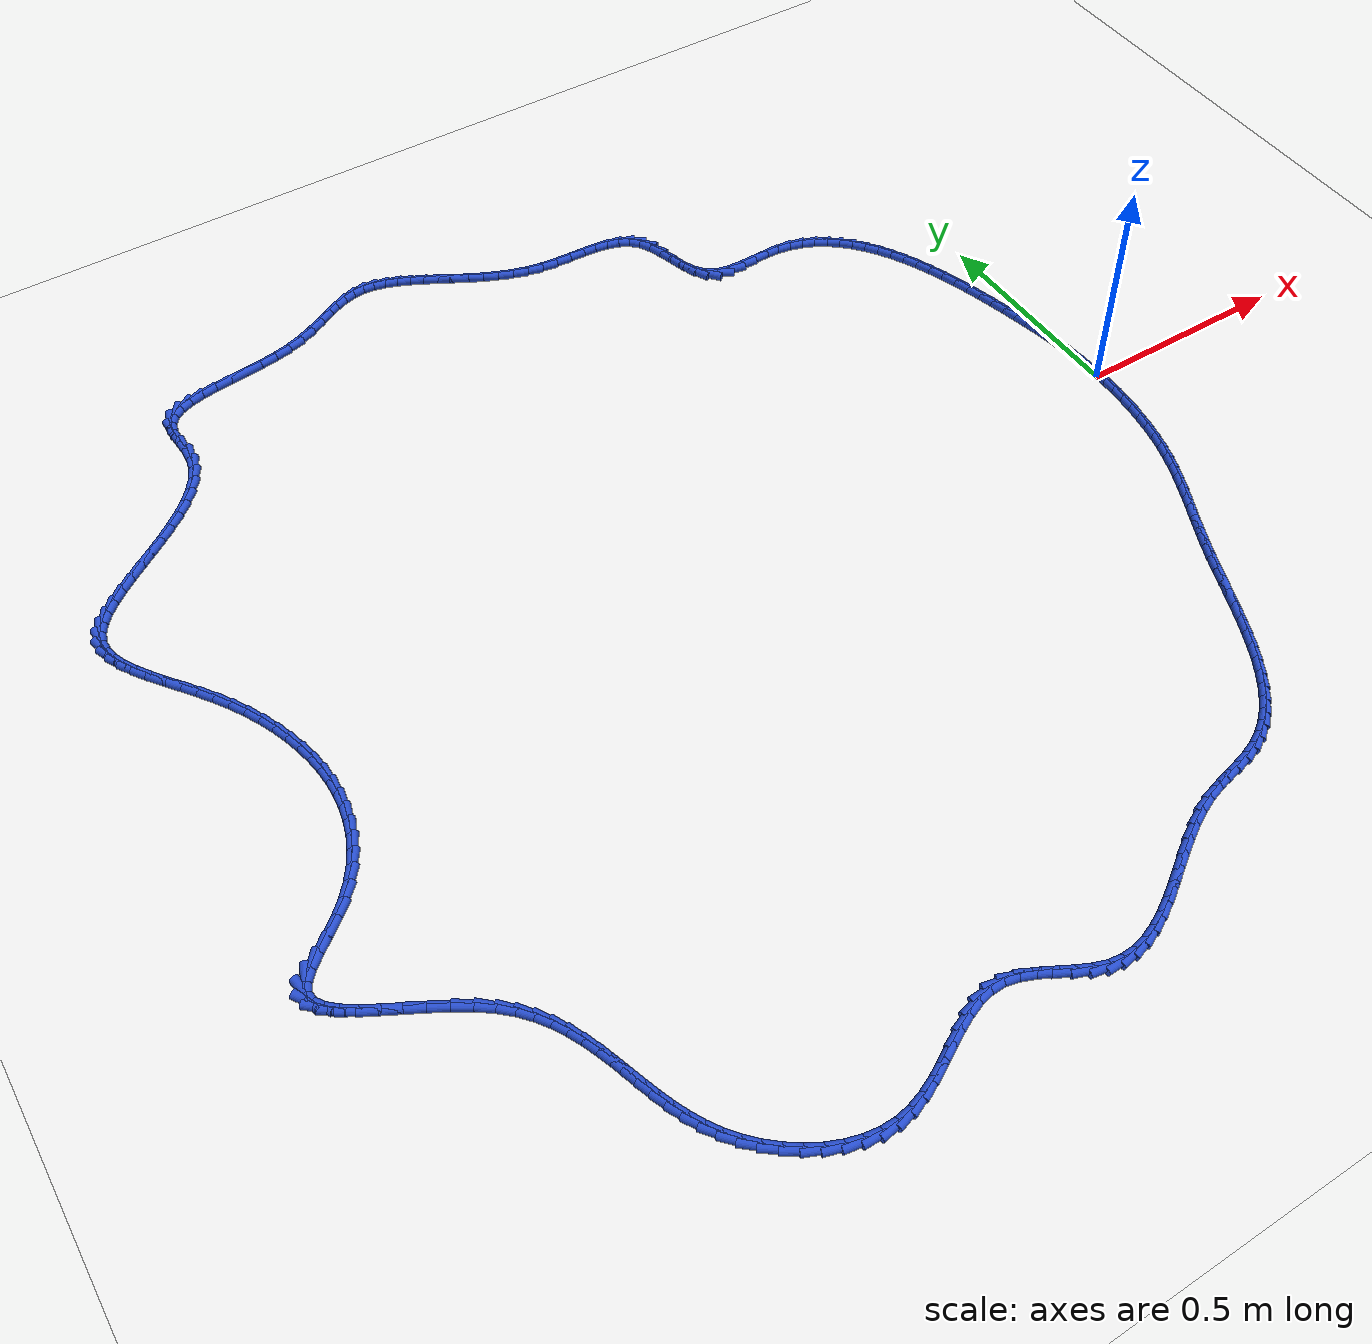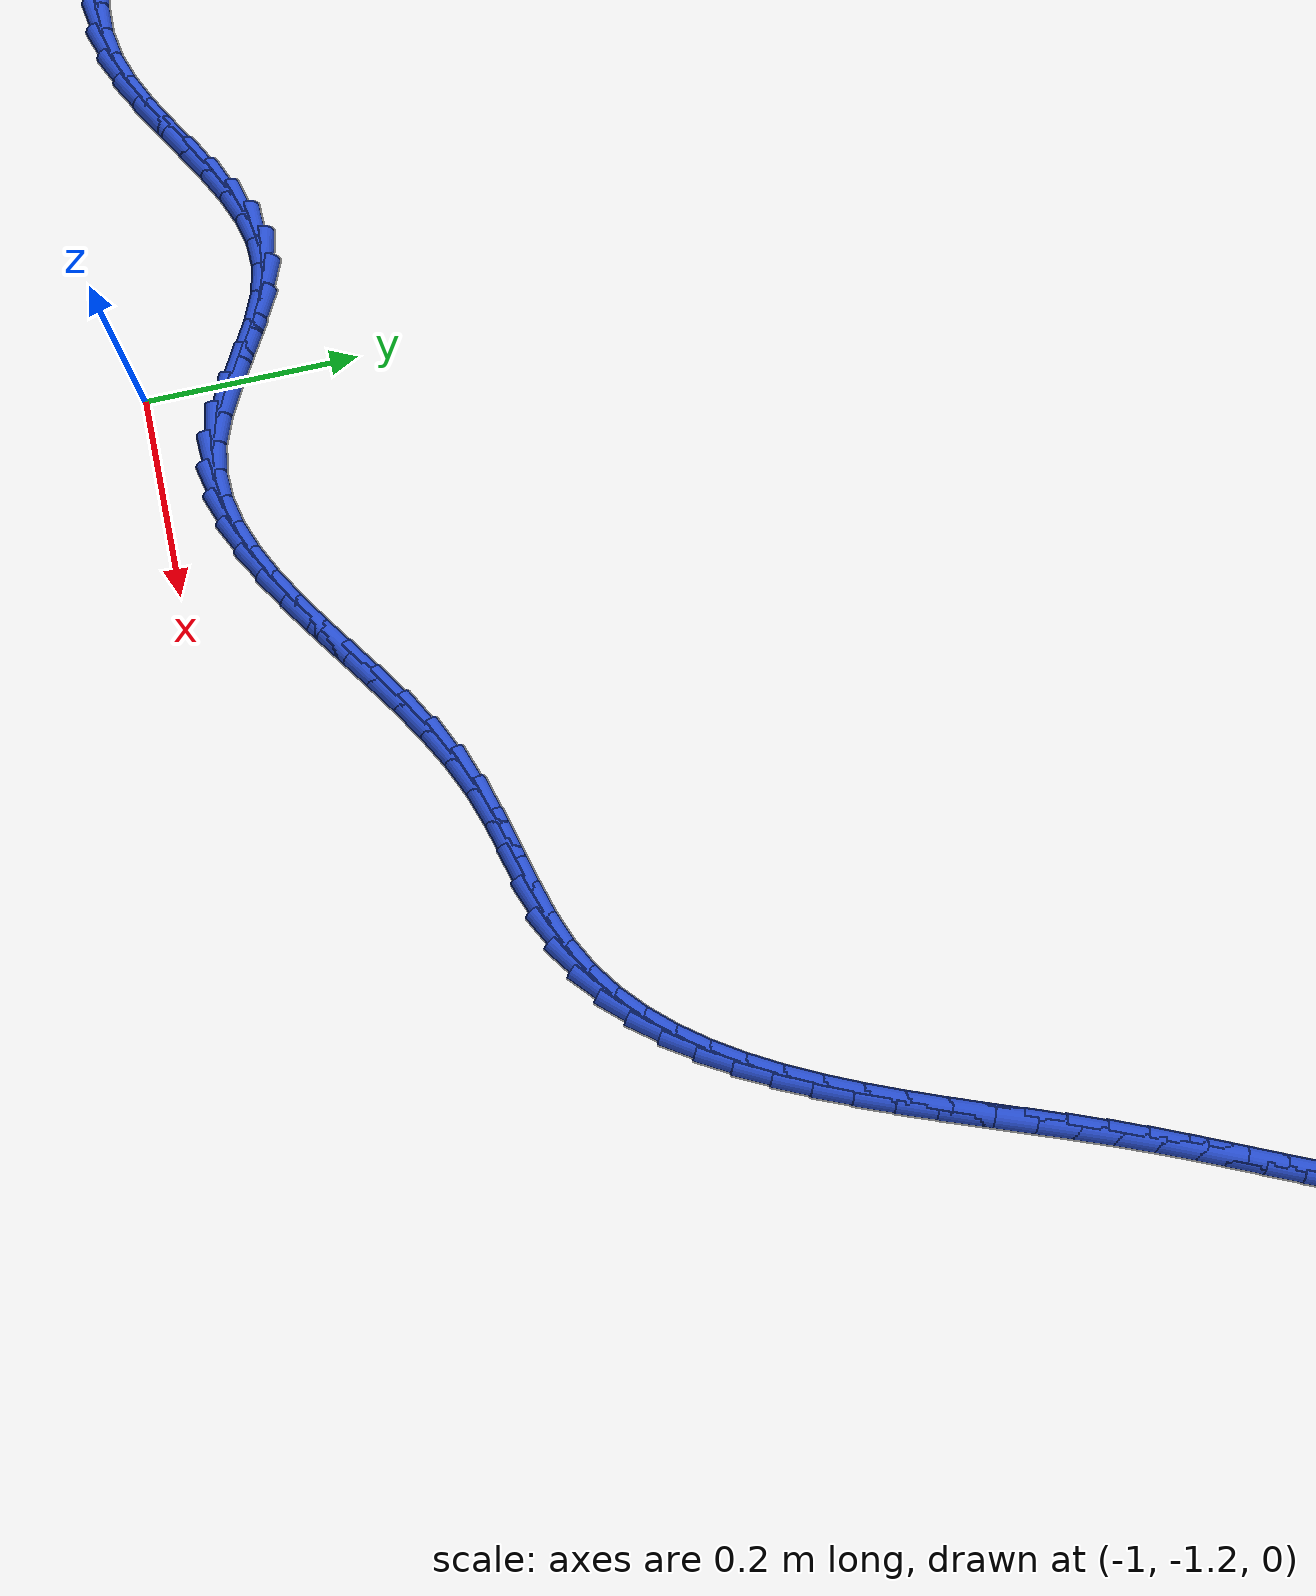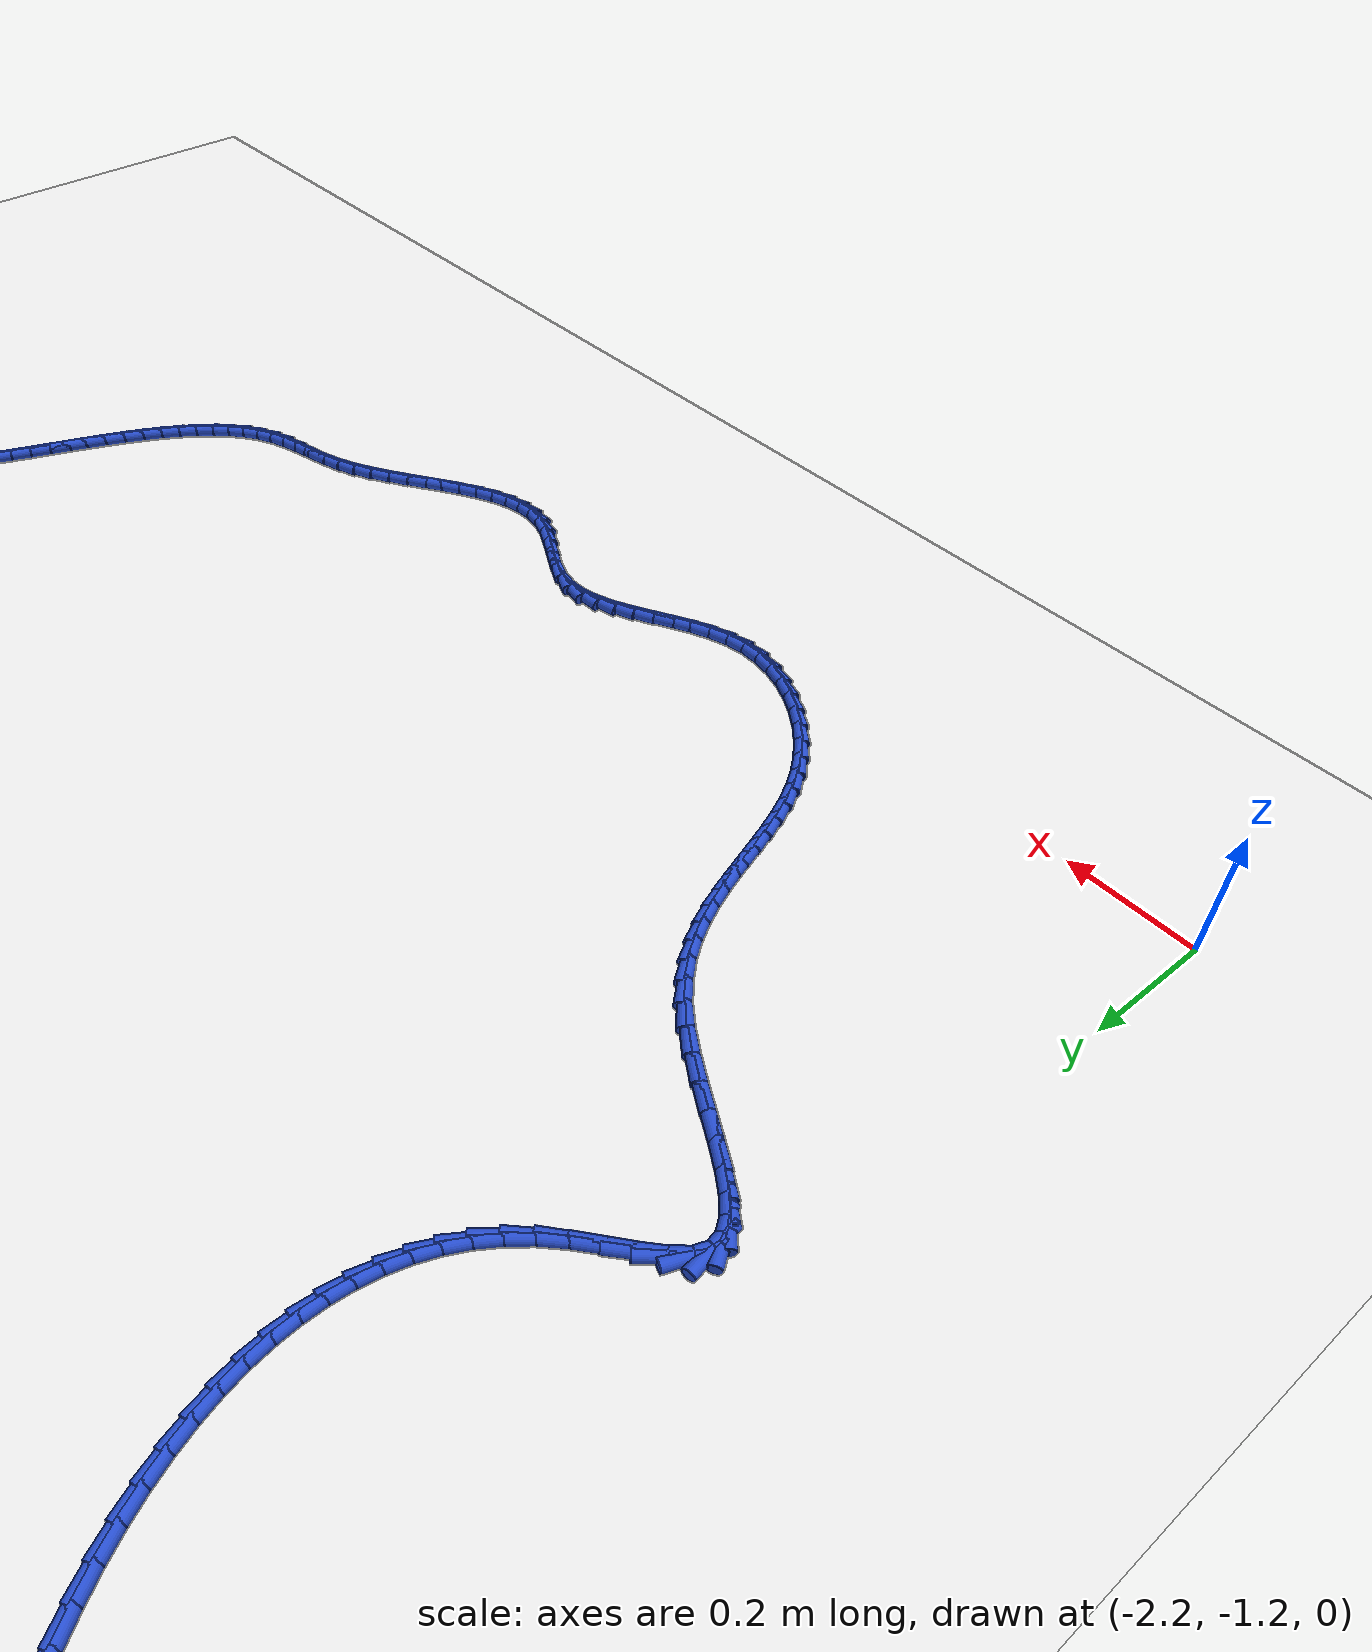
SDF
<sdf version="1.6">
 <world name="default">
  <light name="sun" type="directional">
   <pose>0 0 10 0 -0 0</pose>
   <diffuse>0.8 0.8 0.8 1</diffuse>
   <specular>0.2 0.2 0.2 1</specular>
   <attenuation>
    <range>1000</range>
    <constant>0.9</constant>
    <linear>0.01</linear>
    <quadratic>0.001</quadratic>
   </attenuation>
   <direction>-0.5 0.1 -0.9</direction>
  </light>
  <model name="ground_plane">
   <static>1</static>
   <link name="link">
    <collision name="collision">
     <geometry><plane><normal>0 0 1</normal><size>100 100</size></plane></geometry>
     <surface><friction><ode><mu>100</mu><mu2>50</mu2></ode></friction></surface>
    </collision>
    <visual name="visual">
     <cast_shadows>0</cast_shadows>
     <geometry><plane><normal>0 0 1</normal><size>100 100</size></plane></geometry>
     <material>
      <script><uri>file://media/materials/scripts/gazebo.material</uri><name>Gazebo/WhiteGlow</name></script>
     </material>
    </visual>
   </link>
  </model>
  <gravity>0 0 -9.8</gravity>
  <magnetic_field>6e-06 2.3e-05 -4.2e-05</magnetic_field>
  <atmosphere type="adiabatic"/>
  <physics name="default_physics" default="0" type="ode">
   <max_step_size>0.001</max_step_size>
   <real_time_factor>1</real_time_factor>
   <real_time_update_rate>1000</real_time_update_rate>
  </physics>
  <scene><ambient>0.4 0.4 0.4 1</ambient><background>0.7 0.7 0.7 1</background><shadows>1</shadows></scene>
  <spherical_coordinates>
   <surface_model>EARTH_WGS84</surface_model>
   <latitude_deg>0</latitude_deg>
   <longitude_deg>0</longitude_deg>
   <elevation>0</elevation>
   <heading_deg>0</heading_deg>
  </spherical_coordinates>
  <model name="line">
   <link name="link_0">
    <pose>6.938893903907228e-18 -6.938893903907228e-18 0.01 0 1.57 -1.5380101871183578</pose>
    <collision name="collision">
     <geometry><cylinder><radius>0.01</radius><length>0.08</length></cylinder></geometry>
    </collision>
    <visual name="visual">
     <material>
      <script><name>Gazebo/Blue</name><uri>file://media/materials/scripts/gazebo.material</uri></script>
     </material>
     <geometry><cylinder><radius>0.01</radius><length>0.08</length></cylinder></geometry>
    </visual>
   </link>
   <link name="link_1">
    <pose>-0.0010125075892012242 0.030871117529211917 0.01 0 1.57 -1.5060558207727262</pose>
    <collision name="collision">
     <geometry><cylinder><radius>0.01</radius><length>0.08</length></cylinder></geometry>
    </collision>
    <visual name="visual">
     <material>
      <script><name>Gazebo/Blue</name><uri>file://media/materials/scripts/gazebo.material</uri></script>
     </material>
     <geometry><cylinder><radius>0.01</radius><length>0.08</length></cylinder></geometry>
    </visual>
   </link>
   <link name="link_2">
    <pose>-0.0029968179573395164 0.06147849786982165 0.01 0 1.57 -1.4758701963952163</pose>
    <collision name="collision">
     <geometry><cylinder><radius>0.01</radius><length>0.08</length></cylinder></geometry>
    </collision>
    <visual name="visual">
     <material>
      <script><name>Gazebo/Blue</name><uri>file://media/materials/scripts/gazebo.material</uri></script>
     </material>
     <geometry><cylinder><radius>0.01</radius><length>0.08</length></cylinder></geometry>
    </visual>
   </link>
   <link name="link_3">
    <pose>-0.0059008885439470575 0.0919795042695828 0.01 0 1.57 -1.447963121507701</pose>
    <collision name="collision">
     <geometry><cylinder><radius>0.01</radius><length>0.08</length></cylinder></geometry>
    </collision>
    <visual name="visual">
     <material>
      <script><name>Gazebo/Blue</name><uri>file://media/materials/scripts/gazebo.material</uri></script>
     </material>
     <geometry><cylinder><radius>0.01</radius><length>0.08</length></cylinder></geometry>
    </visual>
   </link>
   <link name="link_4">
    <pose>-0.009672676788556017 0.12253149997624882 0.01 0 1.57 -1.422751854103964</pose>
    <collision name="collision">
     <geometry><cylinder><radius>0.01</radius><length>0.08</length></cylinder></geometry>
    </collision>
    <visual name="visual">
     <material>
      <script><name>Gazebo/Blue</name><uri>file://media/materials/scripts/gazebo.material</uri></script>
     </material>
     <geometry><cylinder><radius>0.01</radius><length>0.08</length></cylinder></geometry>
    </visual>
   </link>
   <link name="link_5">
    <pose>-0.014260140130698585 0.15329184823757327 0.01 0 1.57 -1.4005437216413172</pose>
    <collision name="collision">
     <geometry><cylinder><radius>0.01</radius><length>0.08</length></cylinder></geometry>
    </collision>
    <visual name="visual">
     <material>
      <script><name>Gazebo/Blue</name><uri>file://media/materials/scripts/gazebo.material</uri></script>
     </material>
     <geometry><cylinder><radius>0.01</radius><length>0.08</length></cylinder></geometry>
    </visual>
   </link>
   <link name="link_6">
    <pose>-0.019611236009906934 0.1844179123013097 0.01 0 1.57 -1.3815298972913754</pose>
    <collision name="collision">
     <geometry><cylinder><radius>0.01</radius><length>0.08</length></cylinder></geometry>
    </collision>
    <visual name="visual">
     <material>
      <script><name>Gazebo/Blue</name><uri>file://media/materials/scripts/gazebo.material</uri></script>
     </material>
     <geometry><cylinder><radius>0.01</radius><length>0.08</length></cylinder></geometry>
    </visual>
   </link>
   <link name="link_7">
    <pose>-0.025673921865713246 0.21606705541521157 0.01 0 1.57 -1.3657892270168523</pose>
    <collision name="collision">
     <geometry><cylinder><radius>0.01</radius><length>0.08</length></cylinder></geometry>
    </collision>
    <visual name="visual">
     <material>
      <script><name>Gazebo/Blue</name><uri>file://media/materials/scripts/gazebo.material</uri></script>
     </material>
     <geometry><cylinder><radius>0.01</radius><length>0.08</length></cylinder></geometry>
    </visual>
   </link>
   <link name="link_8">
    <pose>-0.03239615513764969 0.24839664082703242 0.01 0 1.57 -1.3532494051064559</pose>
    <collision name="collision">
     <geometry><cylinder><radius>0.01</radius><length>0.08</length></cylinder></geometry>
    </collision>
    <visual name="visual">
     <material>
      <script><name>Gazebo/Blue</name><uri>file://media/materials/scripts/gazebo.material</uri></script>
     </material>
     <geometry><cylinder><radius>0.01</radius><length>0.08</length></cylinder></geometry>
    </visual>
   </link>
   <link name="link_9">
    <pose>-0.039726936273303745 0.2815608309301771 0.01 0 1.57 -1.3411788114251808</pose>
    <collision name="collision">
     <geometry><cylinder><radius>0.01</radius><length>0.08</length></cylinder></geometry>
    </collision>
    <visual name="visual">
     <material>
      <script><name>Gazebo/Blue</name><uri>file://media/materials/scripts/gazebo.material</uri></script>
     </material>
     <geometry><cylinder><radius>0.01</radius><length>0.08</length></cylinder></geometry>
    </visual>
   </link>
   <link name="link_10">
    <pose>-0.04767034051203258 0.31554477083593147 0.01 0 1.57 -1.3256382477929396</pose>
    <collision name="collision">
     <geometry><cylinder><radius>0.01</radius><length>0.08</length></cylinder></geometry>
    </collision>
    <visual name="visual">
     <material>
      <script><name>Gazebo/Blue</name><uri>file://media/materials/scripts/gazebo.material</uri></script>
     </material>
     <geometry><cylinder><radius>0.01</radius><length>0.08</length></cylinder></geometry>
    </visual>
   </link>
   <link name="link_11">
    <pose>-0.056311752077725735 0.35008407909114053 0.01 0 1.57 -1.306212257859742</pose>
    <collision name="collision">
     <geometry><cylinder><radius>0.01</radius><length>0.08</length></cylinder></geometry>
    </collision>
    <visual name="visual">
     <material>
      <script><name>Gazebo/Blue</name><uri>file://media/materials/scripts/gazebo.material</uri></script>
     </material>
     <geometry><cylinder><radius>0.01</radius><length>0.08</length></cylinder></geometry>
    </visual>
   </link>
   <link name="link_12">
    <pose>-0.06574309594004357 0.3848943015553517 0.01 0 1.57 -1.2826596968596824</pose>
    <collision name="collision">
     <geometry><cylinder><radius>0.01</radius><length>0.08</length></cylinder></geometry>
    </collision>
    <visual name="visual">
     <material>
      <script><name>Gazebo/Blue</name><uri>file://media/materials/scripts/gazebo.material</uri></script>
     </material>
     <geometry><cylinder><radius>0.01</radius><length>0.08</length></cylinder></geometry>
    </visual>
   </link>
   <link name="link_13">
    <pose>-0.07605629706864636 0.41969098408811173 0.01 0 1.57 -1.2546017478848197</pose>
    <collision name="collision">
     <geometry><cylinder><radius>0.01</radius><length>0.08</length></cylinder></geometry>
    </collision>
    <visual name="visual">
     <material>
      <script><name>Gazebo/Blue</name><uri>file://media/materials/scripts/gazebo.material</uri></script>
     </material>
     <geometry><cylinder><radius>0.01</radius><length>0.08</length></cylinder></geometry>
    </visual>
   </link>
   <link name="link_14">
    <pose>-0.08734328043319446 0.45418967254896797 0.01 0 1.57 -1.2215172980234217</pose>
    <collision name="collision">
     <geometry><cylinder><radius>0.01</radius><length>0.08</length></cylinder></geometry>
    </collision>
    <visual name="visual">
     <material>
      <script><name>Gazebo/Blue</name><uri>file://media/materials/scripts/gazebo.material</uri></script>
     </material>
     <geometry><cylinder><radius>0.01</radius><length>0.08</length></cylinder></geometry>
    </visual>
   </link>
   <link name="link_15">
    <pose>-0.0996959710033482 0.48810591279746757 0.01 0 1.57 -1.182733230390341</pose>
    <collision name="collision">
     <geometry><cylinder><radius>0.01</radius><length>0.08</length></cylinder></geometry>
    </collision>
    <visual name="visual">
     <material>
      <script><name>Gazebo/Blue</name><uri>file://media/materials/scripts/gazebo.material</uri></script>
     </material>
     <geometry><cylinder><radius>0.01</radius><length>0.08</length></cylinder></geometry>
    </visual>
   </link>
   <link name="link_16">
    <pose>-0.11320629374876791 0.5211552506931577 0.01 0 1.57 -1.137413754325257</pose>
    <collision name="collision">
     <geometry><cylinder><radius>0.01</radius><length>0.08</length></cylinder></geometry>
    </collision>
    <visual name="visual">
     <material>
      <script><name>Gazebo/Blue</name><uri>file://media/materials/scripts/gazebo.material</uri></script>
     </material>
     <geometry><cylinder><radius>0.01</radius><length>0.08</length></cylinder></geometry>
    </visual>
   </link>
   <link name="link_17">
    <pose>-0.12796617363911383 0.5530532320955854 0.01 0 1.57 -1.084555518454577</pose>
    <collision name="collision">
     <geometry><cylinder><radius>0.01</radius><length>0.08</length></cylinder></geometry>
    </collision>
    <visual name="visual">
     <material>
      <script><name>Gazebo/Blue</name><uri>file://media/materials/scripts/gazebo.material</uri></script>
     </material>
     <geometry><cylinder><radius>0.01</radius><length>0.08</length></cylinder></geometry>
    </visual>
   </link>
   <link name="link_18">
    <pose>-0.14406753564404637 0.5835154028642978 0.01 0 1.57 -1.0230003663762337</pose>
    <collision name="collision">
     <geometry><cylinder><radius>0.01</radius><length>0.08</length></cylinder></geometry>
    </collision>
    <visual name="visual">
     <material>
      <script><name>Gazebo/Blue</name><uri>file://media/materials/scripts/gazebo.material</uri></script>
     </material>
     <geometry><cylinder><radius>0.01</radius><length>0.08</length></cylinder></geometry>
    </visual>
   </link>
   <link name="link_19">
    <pose>-0.16160230473322573 0.612257308858842 0.01 0 1.57 -0.9514858288263982</pose>
    <collision name="collision">
     <geometry><cylinder><radius>0.01</radius><length>0.08</length></cylinder></geometry>
    </collision>
    <visual name="visual">
     <material>
      <script><name>Gazebo/Blue</name><uri>file://media/materials/scripts/gazebo.material</uri></script>
     </material>
     <geometry><cylinder><radius>0.01</radius><length>0.08</length></cylinder></geometry>
    </visual>
   </link>
   <link name="link_20">
    <pose>-0.18066240587631235 0.6389944959387651 0.01 0 1.57 -0.8687640490428645</pose>
    <collision name="collision">
     <geometry><cylinder><radius>0.01</radius><length>0.08</length></cylinder></geometry>
    </collision>
    <visual name="visual">
     <material>
      <script><name>Gazebo/Blue</name><uri>file://media/materials/scripts/gazebo.material</uri></script>
     </material>
     <geometry><cylinder><radius>0.01</radius><length>0.08</length></cylinder></geometry>
    </visual>
   </link>
   <link name="link_21">
    <pose>-0.20133976404296652 0.6634425099636144 0.01 0 1.57 -0.7738274505981849</pose>
    <collision name="collision">
     <geometry><cylinder><radius>0.01</radius><length>0.08</length></cylinder></geometry>
    </collision>
    <visual name="visual">
     <material>
      <script><name>Gazebo/Blue</name><uri>file://media/materials/scripts/gazebo.material</uri></script>
     </material>
     <geometry><cylinder><radius>0.01</radius><length>0.08</length></cylinder></geometry>
    </visual>
   </link>
   <link name="link_22">
    <pose>-0.22372630420284859 0.6853168967929372 0.01 0 1.57 -0.6662689026356294</pose>
    <collision name="collision">
     <geometry><cylinder><radius>0.01</radius><length>0.08</length></cylinder></geometry>
    </collision>
    <visual name="visual">
     <material>
      <script><name>Gazebo/Blue</name><uri>file://media/materials/scripts/gazebo.material</uri></script>
     </material>
     <geometry><cylinder><radius>0.01</radius><length>0.08</length></cylinder></geometry>
    </visual>
   </link>
   <link name="link_23">
    <pose>-0.24791395132561878 0.7043332022862802 0.01 0 1.57 -0.5467489469002796</pose>
    <collision name="collision">
     <geometry><cylinder><radius>0.01</radius><length>0.08</length></cylinder></geometry>
    </collision>
    <visual name="visual">
     <material>
      <script><name>Gazebo/Blue</name><uri>file://media/materials/scripts/gazebo.material</uri></script>
     </material>
     <geometry><cylinder><radius>0.01</radius><length>0.08</length></cylinder></geometry>
    </visual>
   </link>
   <link name="link_24">
    <pose>-0.27399463038093747 0.7202069723031908 0.01 0 1.57 -0.41742559322224176</pose>
    <collision name="collision">
     <geometry><cylinder><radius>0.01</radius><length>0.08</length></cylinder></geometry>
    </collision>
    <visual name="visual">
     <material>
      <script><name>Gazebo/Blue</name><uri>file://media/materials/scripts/gazebo.material</uri></script>
     </material>
     <geometry><cylinder><radius>0.01</radius><length>0.08</length></cylinder></geometry>
    </visual>
   </link>
   <link name="link_25">
    <pose>-0.3020602663384649 0.7326537527032158 0.01 0 1.57 -0.282073997731524</pose>
    <collision name="collision">
     <geometry><cylinder><radius>0.01</radius><length>0.08</length></cylinder></geometry>
    </collision>
    <visual name="visual">
     <material>
      <script><name>Gazebo/Blue</name><uri>file://media/materials/scripts/gazebo.material</uri></script>
     </material>
     <geometry><cylinder><radius>0.01</radius><length>0.08</length></cylinder></geometry>
    </visual>
   </link>
   <link name="link_26">
    <pose>-0.3322027841678616 0.7413890893459028 0.01 0 1.57 -0.14564184642157518</pose>
    <collision name="collision">
     <geometry><cylinder><radius>0.01</radius><length>0.08</length></cylinder></geometry>
    </collision>
    <visual name="visual">
     <material>
      <script><name>Gazebo/Blue</name><uri>file://media/materials/scripts/gazebo.material</uri></script>
     </material>
     <geometry><cylinder><radius>0.01</radius><length>0.08</length></cylinder></geometry>
    </visual>
   </link>
   <link name="link_27">
    <pose>-0.3645141088387877 0.7461285280907985 0.01 0 1.57 -0.02538423099784254</pose>
    <collision name="collision">
     <geometry><cylinder><radius>0.01</radius><length>0.08</length></cylinder></geometry>
    </collision>
    <visual name="visual">
     <material>
      <script><name>Gazebo/Blue</name><uri>file://media/materials/scripts/gazebo.material</uri></script>
     </material>
     <geometry><cylinder><radius>0.01</radius><length>0.08</length></cylinder></geometry>
    </visual>
   </link>
   <link name="link_28">
    <pose>-0.3988312168925125 0.7469998286403554 0.01 0 1.57 0.032893687089779265</pose>
    <collision name="collision">
     <geometry><cylinder><radius>0.01</radius><length>0.08</length></cylinder></geometry>
    </collision>
    <visual name="visual">
     <material>
      <script><name>Gazebo/Blue</name><uri>file://media/materials/scripts/gazebo.material</uri></script>
     </material>
     <geometry><cylinder><radius>0.01</radius><length>0.08</length></cylinder></geometry>
    </visual>
   </link>
   <link name="link_29">
    <pose>-0.4339309369504094 0.7458448528425698 0.01 0 1.57 0.02599234547473987</pose>
    <collision name="collision">
     <geometry><cylinder><radius>0.01</radius><length>0.08</length></cylinder></geometry>
    </collision>
    <visual name="visual">
     <material>
      <script><name>Gazebo/Blue</name><uri>file://media/materials/scripts/gazebo.material</uri></script>
     </material>
     <geometry><cylinder><radius>0.01</radius><length>0.08</length></cylinder></geometry>
    </visual>
   </link>
   <link name="link_30">
    <pose>-0.46831457607238053 0.744950940097012 0.01 0 1.57 -0.051386150759012664</pose>
    <collision name="collision">
     <geometry><cylinder><radius>0.01</radius><length>0.08</length></cylinder></geometry>
    </collision>
    <visual name="visual">
     <material>
      <script><name>Gazebo/Blue</name><uri>file://media/materials/scripts/gazebo.material</uri></script>
     </material>
     <geometry><cylinder><radius>0.01</radius><length>0.08</length></cylinder></geometry>
    </visual>
   </link>
   <link name="link_31">
    <pose>-0.5004834407446201 0.7466054307308524 0.01 0 1.57 -0.22424834764743154</pose>
    <collision name="collision">
     <geometry><cylinder><radius>0.01</radius><length>0.08</length></cylinder></geometry>
    </collision>
    <visual name="visual">
     <material>
      <script><name>Gazebo/Blue</name><uri>file://media/materials/scripts/gazebo.material</uri></script>
     </material>
     <geometry><cylinder><radius>0.01</radius><length>0.08</length></cylinder></geometry>
    </visual>
   </link>
   <link name="link_32">
    <pose>-0.5289388374533226 0.753095665071262 0.01 0 1.57 -0.5298303796738193</pose>
    <collision name="collision">
     <geometry><cylinder><radius>0.01</radius><length>0.08</length></cylinder></geometry>
    </collision>
    <visual name="visual">
     <material>
      <script><name>Gazebo/Blue</name><uri>file://media/materials/scripts/gazebo.material</uri></script>
     </material>
     <geometry><cylinder><radius>0.01</radius><length>0.08</length></cylinder></geometry>
    </visual>
   </link>
   <link name="link_33">
    <pose>-0.5521820760691492 0.7667089785405428 0.01 0 1.57 -0.911510302079967</pose>
    <collision name="collision">
     <geometry><cylinder><radius>0.01</radius><length>0.08</length></cylinder></geometry>
    </collision>
    <visual name="visual">
     <material>
      <script><name>Gazebo/Blue</name><uri>file://media/materials/scripts/gazebo.material</uri></script>
     </material>
     <geometry><cylinder><radius>0.01</radius><length>0.08</length></cylinder></geometry>
    </visual>
   </link>
   <link name="link_34">
    <pose>-0.569331542789127 0.7888384215749312 0.01 0 1.57 -1.158998484451315</pose>
    <collision name="collision">
     <geometry><cylinder><radius>0.01</radius><length>0.08</length></cylinder></geometry>
    </collision>
    <visual name="visual">
     <material>
      <script><name>Gazebo/Blue</name><uri>file://media/materials/scripts/gazebo.material</uri></script>
     </material>
     <geometry><cylinder><radius>0.01</radius><length>0.08</length></cylinder></geometry>
    </visual>
   </link>
   <link name="link_35">
    <pose>-0.5818445615694151 0.8174873878826943 0.01 0 1.57 -1.2743221226054489</pose>
    <collision name="collision">
     <geometry><cylinder><radius>0.01</radius><length>0.08</length></cylinder></geometry>
    </collision>
    <visual name="visual">
     <material>
      <script><name>Gazebo/Blue</name><uri>file://media/materials/scripts/gazebo.material</uri></script>
     </material>
     <geometry><cylinder><radius>0.01</radius><length>0.08</length></cylinder></geometry>
    </visual>
   </link>
   <link name="link_36">
    <pose>-0.591732527082638 0.8498562957510959 0.01 0 1.57 -1.2990886302181817</pose>
    <collision name="collision">
     <geometry><cylinder><radius>0.01</radius><length>0.08</length></cylinder></geometry>
    </collision>
    <visual name="visual">
     <material>
      <script><name>Gazebo/Blue</name><uri>file://media/materials/scripts/gazebo.material</uri></script>
     </material>
     <geometry><cylinder><radius>0.01</radius><length>0.08</length></cylinder></geometry>
    </visual>
   </link>
   <link name="link_37">
    <pose>-0.6010068340014202 0.8831455634674006 0.01 0 1.57 -1.2432682338137393</pose>
    <collision name="collision">
     <geometry><cylinder><radius>0.01</radius><length>0.08</length></cylinder></geometry>
    </collision>
    <visual name="visual">
     <material>
      <script><name>Gazebo/Blue</name><uri>file://media/materials/scripts/gazebo.material</uri></script>
     </material>
     <geometry><cylinder><radius>0.01</radius><length>0.08</length></cylinder></geometry>
    </visual>
   </link>
   <link name="link_38">
    <pose>-0.6116788769983862 0.9145556093188728 0.01 0 1.57 -1.0859640327717612</pose>
    <collision name="collision">
     <geometry><cylinder><radius>0.01</radius><length>0.08</length></cylinder></geometry>
    </collision>
    <visual name="visual">
     <material>
      <script><name>Gazebo/Blue</name><uri>file://media/materials/scripts/gazebo.material</uri></script>
     </material>
     <geometry><cylinder><radius>0.01</radius><length>0.08</length></cylinder></geometry>
    </visual>
   </link>
   <link name="link_39">
    <pose>-0.6257600507461603 0.9412868515927771 0.01 0 1.57 -0.8007553766479872</pose>
    <collision name="collision">
     <geometry><cylinder><radius>0.01</radius><length>0.08</length></cylinder></geometry>
    </collision>
    <visual name="visual">
     <material>
      <script><name>Gazebo/Blue</name><uri>file://media/materials/scripts/gazebo.material</uri></script>
     </material>
     <geometry><cylinder><radius>0.01</radius><length>0.08</length></cylinder></geometry>
    </visual>
   </link>
   <link name="link_40">
    <pose>-0.6449202774188946 0.9610447999694989 0.01 0 1.57 -0.5036832757157778</pose>
    <collision name="collision">
     <geometry><cylinder><radius>0.01</radius><length>0.08</length></cylinder></geometry>
    </collision>
    <visual name="visual">
     <material>
      <script><name>Gazebo/Blue</name><uri>file://media/materials/scripts/gazebo.material</uri></script>
     </material>
     <geometry><cylinder><radius>0.01</radius><length>0.08</length></cylinder></geometry>
    </visual>
   </link>
   <link name="link_41">
    <pose>-0.6689635727987997 0.9742949323937989 0.01 0 1.57 -0.28218743088363357</pose>
    <collision name="collision">
     <geometry><cylinder><radius>0.01</radius><length>0.08</length></cylinder></geometry>
    </collision>
    <visual name="visual">
     <material>
      <script><name>Gazebo/Blue</name><uri>file://media/materials/scripts/gazebo.material</uri></script>
     </material>
     <geometry><cylinder><radius>0.01</radius><length>0.08</length></cylinder></geometry>
    </visual>
   </link>
   <link name="link_42">
    <pose>-0.6970598178792926 0.9824407116418101 0.01 0 1.57 -0.14100774028335877</pose>
    <collision name="collision">
     <geometry><cylinder><radius>0.01</radius><length>0.08</length></cylinder></geometry>
    </collision>
    <visual name="visual">
     <material>
      <script><name>Gazebo/Blue</name><uri>file://media/materials/scripts/gazebo.material</uri></script>
     </material>
     <geometry><cylinder><radius>0.01</radius><length>0.08</length></cylinder></geometry>
    </visual>
   </link>
   <link name="link_43">
    <pose>-0.7283783708529197 0.986886373794168 0.01 0 1.57 -0.06368614505187006</pose>
    <collision name="collision">
     <geometry><cylinder><radius>0.01</radius><length>0.08</length></cylinder></geometry>
    </collision>
    <visual name="visual">
     <material>
      <script><name>Gazebo/Blue</name><uri>file://media/materials/scripts/gazebo.material</uri></script>
     </material>
     <geometry><cylinder><radius>0.01</radius><length>0.08</length></cylinder></geometry>
    </visual>
   </link>
   <link name="link_44">
    <pose>-0.7620885899122277 0.9890361549315072 0.01 0 1.57 -0.03565519345476884</pose>
    <collision name="collision">
     <geometry><cylinder><radius>0.01</radius><length>0.08</length></cylinder></geometry>
    </collision>
    <visual name="visual">
     <material>
      <script><name>Gazebo/Blue</name><uri>file://media/materials/scripts/gazebo.material</uri></script>
     </material>
     <geometry><cylinder><radius>0.01</radius><length>0.08</length></cylinder></geometry>
    </visual>
   </link>
   <link name="link_45">
    <pose>-0.7973598332497623 0.9902942911344629 0.01 0 1.57 -0.04914504568508335</pose>
    <collision name="collision">
     <geometry><cylinder><radius>0.01</radius><length>0.08</length></cylinder></geometry>
    </collision>
    <visual name="visual">
     <material>
      <script><name>Gazebo/Blue</name><uri>file://media/materials/scripts/gazebo.material</uri></script>
     </material>
     <geometry><cylinder><radius>0.01</radius><length>0.08</length></cylinder></geometry>
    </visual>
   </link>
   <link name="link_46">
    <pose>-0.8333614590580708 0.9920650184836695 0.01 0 1.57 -0.1023545462651596</pose>
    <collision name="collision">
     <geometry><cylinder><radius>0.01</radius><length>0.08</length></cylinder></geometry>
    </collision>
    <visual name="visual">
     <material>
      <script><name>Gazebo/Blue</name><uri>file://media/materials/scripts/gazebo.material</uri></script>
     </material>
     <geometry><cylinder><radius>0.01</radius><length>0.08</length></cylinder></geometry>
    </visual>
   </link>
   <link name="link_47">
    <pose>-0.8692628255296989 0.9957525730597627 0.01 0 1.57 -0.19440847672262934</pose>
    <collision name="collision">
     <geometry><cylinder><radius>0.01</radius><length>0.08</length></cylinder></geometry>
    </collision>
    <visual name="visual">
     <material>
      <script><name>Gazebo/Blue</name><uri>file://media/materials/scripts/gazebo.material</uri></script>
     </material>
     <geometry><cylinder><radius>0.01</radius><length>0.08</length></cylinder></geometry>
    </visual>
   </link>
   <link name="link_48">
    <pose>-0.9042827495395587 1.002647830772634 0.01 0 1.57 -0.29183007982551934</pose>
    <collision name="collision">
     <geometry><cylinder><radius>0.01</radius><length>0.08</length></cylinder></geometry>
    </collision>
    <visual name="visual">
     <material>
      <script><name>Gazebo/Blue</name><uri>file://media/materials/scripts/gazebo.material</uri></script>
     </material>
     <geometry><cylinder><radius>0.01</radius><length>0.08</length></cylinder></geometry>
    </visual>
   </link>
   <link name="link_49">
    <pose>-0.9381696962677745 1.0128277042917173 0.01 0 1.57 -0.37195045918545055</pose>
    <collision name="collision">
     <geometry><cylinder><radius>0.01</radius><length>0.08</length></cylinder></geometry>
    </collision>
    <visual name="visual">
     <material>
      <script><name>Gazebo/Blue</name><uri>file://media/materials/scripts/gazebo.material</uri></script>
     </material>
     <geometry><cylinder><radius>0.01</radius><length>0.08</length></cylinder></geometry>
    </visual>
   </link>
   <link name="link_50">
    <pose>-0.9709934871204035 1.0256325521588632 0.01 0 1.57 -0.4341356622220557</pose>
    <collision name="collision">
     <geometry><cylinder><radius>0.01</radius><length>0.08</length></cylinder></geometry>
    </collision>
    <visual name="visual">
     <material>
      <script><name>Gazebo/Blue</name><uri>file://media/materials/scripts/gazebo.material</uri></script>
     </material>
     <geometry><cylinder><radius>0.01</radius><length>0.08</length></cylinder></geometry>
    </visual>
   </link>
   <link name="link_51">
    <pose>-1.0028284550648932 1.0403923923377818 0.01 0 1.57 -0.4786584965775184</pose>
    <collision name="collision">
     <geometry><cylinder><radius>0.01</radius><length>0.08</length></cylinder></geometry>
    </collision>
    <visual name="visual">
     <material>
      <script><name>Gazebo/Blue</name><uri>file://media/materials/scripts/gazebo.material</uri></script>
     </material>
     <geometry><cylinder><radius>0.01</radius><length>0.08</length></cylinder></geometry>
    </visual>
   </link>
   <link name="link_52">
    <pose>-1.0337489330686915 1.056437242792184 0.01 0 1.57 -0.5057915339853803</pose>
    <collision name="collision">
     <geometry><cylinder><radius>0.01</radius><length>0.08</length></cylinder></geometry>
    </collision>
    <visual name="visual">
     <material>
      <script><name>Gazebo/Blue</name><uri>file://media/materials/scripts/gazebo.material</uri></script>
     </material>
     <geometry><cylinder><radius>0.01</radius><length>0.08</length></cylinder></geometry>
    </visual>
   </link>
   <link name="link_53">
    <pose>-1.063829254099246 1.0730971214857805 0.01 0 1.57 -0.515377965592126</pose>
    <collision name="collision">
     <geometry><cylinder><radius>0.01</radius><length>0.08</length></cylinder></geometry>
    </collision>
    <visual name="visual">
     <material>
      <script><name>Gazebo/Blue</name><uri>file://media/materials/scripts/gazebo.material</uri></script>
     </material>
     <geometry><cylinder><radius>0.01</radius><length>0.08</length></cylinder></geometry>
    </visual>
   </link>
   <link name="link_54">
    <pose>-1.093143751124005 1.0897020463822822 0.01 0 1.57 -0.5065195005655194</pose>
    <collision name="collision">
     <geometry><cylinder><radius>0.01</radius><length>0.08</length></cylinder></geometry>
    </collision>
    <visual name="visual">
     <material>
      <script><name>Gazebo/Blue</name><uri>file://media/materials/scripts/gazebo.material</uri></script>
     </material>
     <geometry><cylinder><radius>0.01</radius><length>0.08</length></cylinder></geometry>
    </visual>
   </link>
   <link name="link_55">
    <pose>-1.121766757110416 1.1055820354453991 0.01 0 1.57 -0.47732531902921893</pose>
    <collision name="collision">
     <geometry><cylinder><radius>0.01</radius><length>0.08</length></cylinder></geometry>
    </collision>
    <visual name="visual">
     <material>
      <script><name>Gazebo/Blue</name><uri>file://media/materials/scripts/gazebo.material</uri></script>
     </material>
     <geometry><cylinder><radius>0.01</radius><length>0.08</length></cylinder></geometry>
    </visual>
   </link>
   <link name="link_56">
    <pose>-1.1497726050259265 1.1200671066388417 0.01 0 1.57 -0.4247240327282805</pose>
    <collision name="collision">
     <geometry><cylinder><radius>0.01</radius><length>0.08</length></cylinder></geometry>
    </collision>
    <visual name="visual">
     <material>
      <script><name>Gazebo/Blue</name><uri>file://media/materials/scripts/gazebo.material</uri></script>
     </material>
     <geometry><cylinder><radius>0.01</radius><length>0.08</length></cylinder></geometry>
    </visual>
   </link>
   <link name="link_57">
    <pose>-1.1772356278379854 1.1324872779263222 0.01 0 1.57 -0.34448142181713126</pose>
    <collision name="collision">
     <geometry><cylinder><radius>0.01</radius><length>0.08</length></cylinder></geometry>
    </collision>
    <visual name="visual">
     <material>
      <script><name>Gazebo/Blue</name><uri>file://media/materials/scripts/gazebo.material</uri></script>
     </material>
     <geometry><cylinder><radius>0.01</radius><length>0.08</length></cylinder></geometry>
    </visual>
   </link>
   <link name="link_58">
    <pose>-1.2042301585140398 1.1421725672715501 0.01 0 1.57 -0.23185690156513195</pose>
    <collision name="collision">
     <geometry><cylinder><radius>0.01</radius><length>0.08</length></cylinder></geometry>
    </collision>
    <visual name="visual">
     <material>
      <script><name>Gazebo/Blue</name><uri>file://media/materials/scripts/gazebo.material</uri></script>
     </material>
     <geometry><cylinder><radius>0.01</radius><length>0.08</length></cylinder></geometry>
    </visual>
   </link>
   <link name="link_59">
    <pose>-1.2308305300215383 1.1484529926382365 0.01 0 1.57 -0.08372820688072695</pose>
    <collision name="collision">
     <geometry><cylinder><radius>0.01</radius><length>0.08</length></cylinder></geometry>
    </collision>
    <visual name="visual">
     <material>
      <script><name>Gazebo/Blue</name><uri>file://media/materials/scripts/gazebo.material</uri></script>
     </material>
     <geometry><cylinder><radius>0.01</radius><length>0.08</length></cylinder></geometry>
    </visual>
   </link>
   <link name="link_60">
    <pose>-1.2571110753279273 1.1506585719900917 0.01 0 1.57 0.09720884950132962</pose>
    <collision name="collision">
     <geometry><cylinder><radius>0.01</radius><length>0.08</length></cylinder></geometry>
    </collision>
    <visual name="visual">
     <material>
      <script><name>Gazebo/Blue</name><uri>file://media/materials/scripts/gazebo.material</uri></script>
     </material>
     <geometry><cylinder><radius>0.01</radius><length>0.08</length></cylinder></geometry>
    </visual>
   </link>
   <link name="link_61">
    <pose>-1.2831462005080072 1.148119725387512 0.01 0 1.57 0.2819185565437472</pose>
    <collision name="collision">
     <geometry><cylinder><radius>0.01</radius><length>0.08</length></cylinder></geometry>
    </collision>
    <visual name="visual">
     <material>
      <script><name>Gazebo/Blue</name><uri>file://media/materials/scripts/gazebo.material</uri></script>
     </material>
     <geometry><cylinder><radius>0.01</radius><length>0.08</length></cylinder></geometry>
    </visual>
   </link>
   <link name="link_62">
    <pose>-1.3090900669652124 1.1406055340218775 0.01 0 1.57 0.4113120938510309</pose>
    <collision name="collision">
     <geometry><cylinder><radius>0.01</radius><length>0.08</length></cylinder></geometry>
    </collision>
    <visual name="visual">
     <material>
      <script><name>Gazebo/Blue</name><uri>file://media/materials/scripts/gazebo.material</uri></script>
     </material>
     <geometry><cylinder><radius>0.01</radius><length>0.08</length></cylinder></geometry>
    </visual>
   </link>
   <link name="link_63">
    <pose>-1.335328716937232 1.1291604435115823 0.01 0 1.57 0.481885160426395</pose>
    <collision name="collision">
     <geometry><cylinder><radius>0.01</radius><length>0.08</length></cylinder></geometry>
    </collision>
    <visual name="visual">
     <material>
      <script><name>Gazebo/Blue</name><uri>file://media/materials/scripts/gazebo.material</uri></script>
     </material>
     <geometry><cylinder><radius>0.01</radius><length>0.08</length></cylinder></geometry>
    </visual>
   </link>
   <link name="link_64">
    <pose>-1.3622900993055573 1.1150593896012648 0.01 0 1.57 0.503401445067003</pose>
    <collision name="collision">
     <geometry><cylinder><radius>0.01</radius><length>0.08</length></cylinder></geometry>
    </collision>
    <visual name="visual">
     <material>
      <script><name>Gazebo/Blue</name><uri>file://media/materials/scripts/gazebo.material</uri></script>
     </material>
     <geometry><cylinder><radius>0.01</radius><length>0.08</length></cylinder></geometry>
    </visual>
   </link>
   <link name="link_65">
    <pose>-1.3904021629516803 1.099577308035563 0.01 0 1.57 0.48346176687973663</pose>
    <collision name="collision">
     <geometry><cylinder><radius>0.01</radius><length>0.08</length></cylinder></geometry>
    </collision>
    <visual name="visual">
     <material>
      <script><name>Gazebo/Blue</name><uri>file://media/materials/scripts/gazebo.material</uri></script>
     </material>
     <geometry><cylinder><radius>0.01</radius><length>0.08</length></cylinder></geometry>
    </visual>
   </link>
   <link name="link_66">
    <pose>-1.4200928567570923 1.0839891345591153 0.01 0 1.57 0.42692756879477745</pose>
    <collision name="collision">
     <geometry><cylinder><radius>0.01</radius><length>0.08</length></cylinder></geometry>
    </collision>
    <visual name="visual">
     <material>
      <script><name>Gazebo/Blue</name><uri>file://media/materials/scripts/gazebo.material</uri></script>
     </material>
     <geometry><cylinder><radius>0.01</radius><length>0.08</length></cylinder></geometry>
    </visual>
   </link>
   <link name="link_67">
    <pose>-1.4517901296032836 1.0695698049165578 0.01 0 1.57 0.3375384432785946</pose>
    <collision name="collision">
     <geometry><cylinder><radius>0.01</radius><length>0.08</length></cylinder></geometry>
    </collision>
    <visual name="visual">
     <material>
      <script><name>Gazebo/Blue</name><uri>file://media/materials/scripts/gazebo.material</uri></script>
     </material>
     <geometry><cylinder><radius>0.01</radius><length>0.08</length></cylinder></geometry>
    </visual>
   </link>
   <link name="link_68">
    <pose>-1.4859199372988179 1.0575912761672759 0.01 0 1.57 0.23822882449814034</pose>
    <collision name="collision">
     <geometry><cylinder><radius>0.01</radius><length>0.08</length></cylinder></geometry>
    </collision>
    <visual name="visual">
     <material>
      <script><name>Gazebo/Blue</name><uri>file://media/materials/scripts/gazebo.material</uri></script>
     </material>
     <geometry><cylinder><radius>0.01</radius><length>0.08</length></cylinder></geometry>
    </visual>
   </link>
   <link name="link_69">
    <pose>-1.522495841061396 1.0487091738411023 0.01 0 1.57 0.16883211485869765</pose>
    <collision name="collision">
     <geometry><cylinder><radius>0.01</radius><length>0.08</length></cylinder></geometry>
    </collision>
    <visual name="visual">
     <material>
      <script><name>Gazebo/Blue</name><uri>file://media/materials/scripts/gazebo.material</uri></script>
     </material>
     <geometry><cylinder><radius>0.01</radius><length>0.08</length></cylinder></geometry>
    </visual>
   </link>
   <link name="link_70">
    <pose>-1.560616224300529 1.042211372893946 0.01 0 1.57 0.12892711441760724</pose>
    <collision name="collision">
     <geometry><cylinder><radius>0.01</radius><length>0.08</length></cylinder></geometry>
    </collision>
    <visual name="visual">
     <material>
      <script><name>Gazebo/Blue</name><uri>file://media/materials/scripts/gazebo.material</uri></script>
     </material>
     <geometry><cylinder><radius>0.01</radius><length>0.08</length></cylinder></geometry>
    </visual>
   </link>
   <link name="link_71">
    <pose>-1.5992564011893233 1.0372018189761578 0.01 0 1.57 0.11532002854234076</pose>
    <collision name="collision">
     <geometry><cylinder><radius>0.01</radius><length>0.08</length></cylinder></geometry>
    </collision>
    <visual name="visual">
     <material>
      <script><name>Gazebo/Blue</name><uri>file://media/materials/scripts/gazebo.material</uri></script>
     </material>
     <geometry><cylinder><radius>0.01</radius><length>0.08</length></cylinder></geometry>
    </visual>
   </link>
   <link name="link_72">
    <pose>-1.637391685900886 1.032784457738088 0.01 0 1.57 0.12826695757120316</pose>
    <collision name="collision">
     <geometry><cylinder><radius>0.01</radius><length>0.08</length></cylinder></geometry>
    </collision>
    <visual name="visual">
     <material>
      <script><name>Gazebo/Blue</name><uri>file://media/materials/scripts/gazebo.material</uri></script>
     </material>
     <geometry><cylinder><radius>0.01</radius><length>0.08</length></cylinder></geometry>
    </visual>
   </link>
   <link name="link_73">
    <pose>-1.6739973926083238 1.0280632348300873 0.01 0 1.57 0.17216655258966776</pose>
    <collision name="collision">
     <geometry><cylinder><radius>0.01</radius><length>0.08</length></cylinder></geometry>
    </collision>
    <visual name="visual">
     <material>
      <script><name>Gazebo/Blue</name><uri>file://media/materials/scripts/gazebo.material</uri></script>
     </material>
     <geometry><cylinder><radius>0.01</radius><length>0.08</length></cylinder></geometry>
    </visual>
   </link>
   <link name="link_74">
    <pose>-1.7080488354847438 1.0221420959025063 0.01 0 1.57 0.25726331811636144</pose>
    <collision name="collision">
     <geometry><cylinder><radius>0.01</radius><length>0.08</length></cylinder></geometry>
    </collision>
    <visual name="visual">
     <material>
      <script><name>Gazebo/Blue</name><uri>file://media/materials/scripts/gazebo.material</uri></script>
     </material>
     <geometry><cylinder><radius>0.01</radius><length>0.08</length></cylinder></geometry>
    </visual>
   </link>
   <link name="link_75">
    <pose>-1.7385213287032533 1.0141249866056958 0.01 0 1.57 0.40235740940196135</pose>
    <collision name="collision">
     <geometry><cylinder><radius>0.01</radius><length>0.08</length></cylinder></geometry>
    </collision>
    <visual name="visual">
     <material>
      <script><name>Gazebo/Blue</name><uri>file://media/materials/scripts/gazebo.material</uri></script>
     </material>
     <geometry><cylinder><radius>0.01</radius><length>0.08</length></cylinder></geometry>
    </visual>
   </link>
   <link name="link_76">
    <pose>-1.7643901864369576 1.003115852590006 0.01 0 1.57 0.634486448030301</pose>
    <collision name="collision">
     <geometry><cylinder><radius>0.01</radius><length>0.08</length></cylinder></geometry>
    </collision>
    <visual name="visual">
     <material>
      <script><name>Gazebo/Blue</name><uri>file://media/materials/scripts/gazebo.material</uri></script>
     </material>
     <geometry><cylinder><radius>0.01</radius><length>0.08</length></cylinder></geometry>
    </visual>
   </link>
   <link name="link_77">
    <pose>-1.7846307228589662 0.9882186395057875 0.01 0 1.57 0.9665586676599686</pose>
    <collision name="collision">
     <geometry><cylinder><radius>0.01</radius><length>0.08</length></cylinder></geometry>
    </collision>
    <visual name="visual">
     <material>
      <script><name>Gazebo/Blue</name><uri>file://media/materials/scripts/gazebo.material</uri></script>
     </material>
     <geometry><cylinder><radius>0.01</radius><length>0.08</length></cylinder></geometry>
    </visual>
   </link>
   <link name="link_78">
    <pose>-1.7982182521423837 0.9685372930033913 0.01 0 1.57 1.3397652919131398</pose>
    <collision name="collision">
     <geometry><cylinder><radius>0.01</radius><length>0.08</length></cylinder></geometry>
    </collision>
    <visual name="visual">
     <material>
      <script><name>Gazebo/Blue</name><uri>file://media/materials/scripts/gazebo.material</uri></script>
     </material>
     <geometry><cylinder><radius>0.01</radius><length>0.08</length></cylinder></geometry>
    </visual>
   </link>
   <link name="link_79">
    <pose>-1.8041770512477864 0.9432056214771167 0.01 0 1.57 -1.5601213194515915</pose>
    <collision name="collision">
     <geometry><cylinder><radius>0.01</radius><length>0.08</length></cylinder></geometry>
    </collision>
    <visual name="visual">
     <material>
      <script><name>Gazebo/Blue</name><uri>file://media/materials/scripts/gazebo.material</uri></script>
     </material>
     <geometry><cylinder><radius>0.01</radius><length>0.08</length></cylinder></geometry>
    </visual>
   </link>
   <link name="link_80">
    <pose>-1.8038521692573324 0.9127728883477183 0.01 0 1.57 -1.5107689227942482</pose>
    <collision name="collision">
     <geometry><cylinder><radius>0.01</radius><length>0.08</length></cylinder></geometry>
    </collision>
    <visual name="visual">
     <material>
      <script><name>Gazebo/Blue</name><uri>file://media/materials/scripts/gazebo.material</uri></script>
     </material>
     <geometry><cylinder><radius>0.01</radius><length>0.08</length></cylinder></geometry>
    </visual>
   </link>
   <link name="link_81">
    <pose>-1.8018698867729603 0.8797896029163349 0.01 0 1.57 1.5339193391813333</pose>
    <collision name="collision">
     <geometry><cylinder><radius>0.01</radius><length>0.08</length></cylinder></geometry>
    </collision>
    <visual name="visual">
     <material>
      <script><name>Gazebo/Blue</name><uri>file://media/materials/scripts/gazebo.material</uri></script>
     </material>
     <geometry><cylinder><radius>0.01</radius><length>0.08</length></cylinder></geometry>
    </visual>
   </link>
   <link name="link_82">
    <pose>-1.8030816107078962 0.8469459601972049 0.01 0 1.57 1.3391086376146026</pose>
    <collision name="collision">
     <geometry><cylinder><radius>0.01</radius><length>0.08</length></cylinder></geometry>
    </collision>
    <visual name="visual">
     <material>
      <script><name>Gazebo/Blue</name><uri>file://media/materials/scripts/gazebo.material</uri></script>
     </material>
     <geometry><cylinder><radius>0.01</radius><length>0.08</length></cylinder></geometry>
    </visual>
   </link>
   <link name="link_83">
    <pose>-1.8103951862088816 0.815946287509181 0.01 0 1.57 1.1532130733497599</pose>
    <collision name="collision">
     <geometry><cylinder><radius>0.01</radius><length>0.08</length></cylinder></geometry>
    </collision>
    <visual name="visual">
     <material>
      <script><name>Gazebo/Blue</name><uri>file://media/materials/scripts/gazebo.material</uri></script>
     </material>
     <geometry><cylinder><radius>0.01</radius><length>0.08</length></cylinder></geometry>
    </visual>
   </link>
   <link name="link_84">
    <pose>-1.823335971722134 0.7867791527722598 0.01 0 1.57 0.9978079981529836</pose>
    <collision name="collision">
     <geometry><cylinder><radius>0.01</radius><length>0.08</length></cylinder></geometry>
    </collision>
    <visual name="visual">
     <material>
      <script><name>Gazebo/Blue</name><uri>file://media/materials/scripts/gazebo.material</uri></script>
     </material>
     <geometry><cylinder><radius>0.01</radius><length>0.08</length></cylinder></geometry>
    </visual>
   </link>
   <link name="link_85">
    <pose>-1.841090363336493 0.7592611859501264 0.01 0 1.57 0.8750564170237828</pose>
    <collision name="collision">
     <geometry><cylinder><radius>0.01</radius><length>0.08</length></cylinder></geometry>
    </collision>
    <visual name="visual">
     <material>
      <script><name>Gazebo/Blue</name><uri>file://media/materials/scripts/gazebo.material</uri></script>
     </material>
     <geometry><cylinder><radius>0.01</radius><length>0.08</length></cylinder></geometry>
    </visual>
   </link>
   <link name="link_86">
    <pose>-1.8628447571407964 0.7332090170064669 0.01 0 1.57 0.7819572365847536</pose>
    <collision name="collision">
     <geometry><cylinder><radius>0.01</radius><length>0.08</length></cylinder></geometry>
    </collision>
    <visual name="visual">
     <material>
      <script><name>Gazebo/Blue</name><uri>file://media/materials/scripts/gazebo.material</uri></script>
     </material>
     <geometry><cylinder><radius>0.01</radius><length>0.08</length></cylinder></geometry>
    </visual>
   </link>
   <link name="link_87">
    <pose>-1.8877855492238849 0.7084392759049671 0.01 0 1.57 0.7140678746551105</pose>
    <collision name="collision">
     <geometry><cylinder><radius>0.01</radius><length>0.08</length></cylinder></geometry>
    </collision>
    <visual name="visual">
     <material>
      <script><name>Gazebo/Blue</name><uri>file://media/materials/scripts/gazebo.material</uri></script>
     </material>
     <geometry><cylinder><radius>0.01</radius><length>0.08</length></cylinder></geometry>
    </visual>
   </link>
   <link name="link_88">
    <pose>-1.9150991356745963 0.6847685926093123 0.01 0 1.57 0.6674502998512541</pose>
    <collision name="collision">
     <geometry><cylinder><radius>0.01</radius><length>0.08</length></cylinder></geometry>
    </collision>
    <visual name="visual">
     <material>
      <script><name>Gazebo/Blue</name><uri>file://media/materials/scripts/gazebo.material</uri></script>
     </material>
     <geometry><cylinder><radius>0.01</radius><length>0.08</length></cylinder></geometry>
    </visual>
   </link>
   <link name="link_89">
    <pose>-1.9439719125817696 0.6620135970831892 0.01 0 1.57 0.639359087255914</pose>
    <collision name="collision">
     <geometry><cylinder><radius>0.01</radius><length>0.08</length></cylinder></geometry>
    </collision>
    <visual name="visual">
     <material>
      <script><name>Gazebo/Blue</name><uri>file://media/materials/scripts/gazebo.material</uri></script>
     </material>
     <geometry><cylinder><radius>0.01</radius><length>0.08</length></cylinder></geometry>
    </visual>
   </link>
   <link name="link_90">
    <pose>-1.9735902760342439 0.6399909192902824 0.01 0 1.57 0.6284103750160742</pose>
    <collision name="collision">
     <geometry><cylinder><radius>0.01</radius><length>0.08</length></cylinder></geometry>
    </collision>
    <visual name="visual">
     <material>
      <script><name>Gazebo/Blue</name><uri>file://media/materials/scripts/gazebo.material</uri></script>
     </material>
     <geometry><cylinder><radius>0.01</radius><length>0.08</length></cylinder></geometry>
    </visual>
   </link>
   <link name="link_91">
    <pose>-2.003140622120858 0.6185171891942787 0.01 0 1.57 0.634661056065516</pose>
    <collision name="collision">
     <geometry><cylinder><radius>0.01</radius><length>0.08</length></cylinder></geometry>
    </collision>
    <visual name="visual">
     <material>
      <script><name>Gazebo/Blue</name><uri>file://media/materials/scripts/gazebo.material</uri></script>
     </material>
     <geometry><cylinder><radius>0.01</radius><length>0.08</length></cylinder></geometry>
    </visual>
   </link>
   <link name="link_92">
    <pose>-2.0318093469304515 0.5974090367588631 0.01 0 1.57 0.6598074531961498</pose>
    <collision name="collision">
     <geometry><cylinder><radius>0.01</radius><length>0.08</length></cylinder></geometry>
    </collision>
    <visual name="visual">
     <material>
      <script><name>Gazebo/Blue</name><uri>file://media/materials/scripts/gazebo.material</uri></script>
     </material>
     <geometry><cylinder><radius>0.01</radius><length>0.08</length></cylinder></geometry>
    </visual>
   </link>
   <link name="link_93">
    <pose>-2.0587828465518623 0.5764830919477222 0.01 0 1.57 0.7076213629044643</pose>
    <collision name="collision">
     <geometry><cylinder><radius>0.01</radius><length>0.08</length></cylinder></geometry>
    </collision>
    <visual name="visual">
     <material>
      <script><name>Gazebo/Blue</name><uri>file://media/materials/scripts/gazebo.material</uri></script>
     </material>
     <geometry><cylinder><radius>0.01</radius><length>0.08</length></cylinder></geometry>
    </visual>
   </link>
   <link name="link_94">
    <pose>-2.08324751707393 0.5555559847245408 0.01 0 1.57 0.7846740207454632</pose>
    <collision name="collision">
     <geometry><cylinder><radius>0.01</radius><length>0.08</length></cylinder></geometry>
    </collision>
    <visual name="visual">
     <material>
      <script><name>Gazebo/Blue</name><uri>file://media/materials/scripts/gazebo.material</uri></script>
     </material>
     <geometry><cylinder><radius>0.01</radius><length>0.08</length></cylinder></geometry>
    </visual>
   </link>
   <link name="link_95">
    <pose>-2.1043897545854935 0.5344443450530056 0.01 0 1.57 0.9011126494347083</pose>
    <collision name="collision">
     <geometry><cylinder><radius>0.01</radius><length>0.08</length></cylinder></geometry>
    </collision>
    <visual name="visual">
     <material>
      <script><name>Gazebo/Blue</name><uri>file://media/materials/scripts/gazebo.material</uri></script>
     </material>
     <geometry><cylinder><radius>0.01</radius><length>0.08</length></cylinder></geometry>
    </visual>
   </link>
   <link name="link_96">
    <pose>-2.121395955175392 0.5129648028968018 0.01 0 1.57 1.070060030570087</pose>
    <collision name="collision">
     <geometry><cylinder><radius>0.01</radius><length>0.08</length></cylinder></geometry>
    </collision>
    <visual name="visual">
     <material>
      <script><name>Gazebo/Blue</name><uri>file://media/materials/scripts/gazebo.material</uri></script>
     </material>
     <geometry><cylinder><radius>0.01</radius><length>0.08</length></cylinder></geometry>
    </visual>
   </link>
   <link name="link_97">
    <pose>-2.133452514932463 0.49093398821961565 0.01 0 1.57 1.3010905463776898</pose>
    <collision name="collision">
     <geometry><cylinder><radius>0.01</radius><length>0.08</length></cylinder></geometry>
    </collision>
    <visual name="visual">
     <material>
      <script><name>Gazebo/Blue</name><uri>file://media/materials/scripts/gazebo.material</uri></script>
     </material>
     <geometry><cylinder><radius>0.01</radius><length>0.08</length></cylinder></geometry>
    </visual>
   </link>
   <link name="link_98">
    <pose>-2.139745829945548 0.46816853098513256 0.01 0 1.57 -1.5670894802264577</pose>
    <collision name="collision">
     <geometry><cylinder><radius>0.01</radius><length>0.08</length></cylinder></geometry>
    </collision>
    <visual name="visual">
     <material>
      <script><name>Gazebo/Blue</name><uri>file://media/materials/scripts/gazebo.material</uri></script>
     </material>
     <geometry><cylinder><radius>0.01</radius><length>0.08</length></cylinder></geometry>
    </visual>
   </link>
   <link name="link_99">
    <pose>-2.13965812268142 0.44450775604122195 0.01 0 1.57 -1.3330248739087511</pose>
    <collision name="collision">
     <geometry><cylinder><radius>0.01</radius><length>0.08</length></cylinder></geometry>
    </collision>
    <visual name="visual">
     <material>
      <script><name>Gazebo/Blue</name><uri>file://media/materials/scripts/gazebo.material</uri></script>
     </material>
     <geometry><cylinder><radius>0.01</radius><length>0.08</length></cylinder></geometry>
    </visual>
   </link>
   <link name="link_100">
    <pose>-2.133699546782632 0.4199217074354418 0.01 0 1.57 -1.1662346618241064</pose>
    <collision name="collision">
     <geometry><cylinder><radius>0.01</radius><length>0.08</length></cylinder></geometry>
    </collision>
    <visual name="visual">
     <material>
      <script><name>Gazebo/Blue</name><uri>file://media/materials/scripts/gazebo.material</uri></script>
     </material>
     <geometry><cylinder><radius>0.01</radius><length>0.08</length></cylinder></geometry>
    </visual>
   </link>
   <link name="link_101">
    <pose>-2.1227832620979683 0.3944271347678499 0.01 0 1.57 -1.0550150074844977</pose>
    <collision name="collision">
     <geometry><cylinder><radius>0.01</radius><length>0.08</length></cylinder></geometry>
    </collision>
    <visual name="visual">
     <material>
      <script><name>Gazebo/Blue</name><uri>file://media/materials/scripts/gazebo.material</uri></script>
     </material>
     <geometry><cylinder><radius>0.01</radius><length>0.08</length></cylinder></geometry>
    </visual>
   </link>
   <link name="link_102">
    <pose>-2.1078229325525846 0.36804084605737103 0.01 0 1.57 -0.9849152137478456</pose>
    <collision name="collision">
     <geometry><cylinder><radius>0.01</radius><length>0.08</length></cylinder></geometry>
    </collision>
    <visual name="visual">
     <material>
      <script><name>Gazebo/Blue</name><uri>file://media/materials/scripts/gazebo.material</uri></script>
     </material>
     <geometry><cylinder><radius>0.01</radius><length>0.08</length></cylinder></geometry>
    </visual>
   </link>
   <link name="link_103">
    <pose>-2.089732222071634 0.3407796493229285 0.01 0 1.57 -0.9453335717010565</pose>
    <collision name="collision">
     <geometry><cylinder><radius>0.01</radius><length>0.08</length></cylinder></geometry>
    </collision>
    <visual name="visual">
     <material>
      <script><name>Gazebo/Blue</name><uri>file://media/materials/scripts/gazebo.material</uri></script>
     </material>
     <geometry><cylinder><radius>0.01</radius><length>0.08</length></cylinder></geometry>
    </visual>
   </link>
   <link name="link_104">
    <pose>-2.069424794580273 0.31266035258344704 0.01 0 1.57 -0.9297296772844875</pose>
    <collision name="collision">
     <geometry><cylinder><radius>0.01</radius><length>0.08</length></cylinder></geometry>
    </collision>
    <visual name="visual">
     <material>
      <script><name>Gazebo/Blue</name><uri>file://media/materials/scripts/gazebo.material</uri></script>
     </material>
     <geometry><cylinder><radius>0.01</radius><length>0.08</length></cylinder></geometry>
    </visual>
   </link>
   <link name="link_105">
    <pose>-2.047814314003652 0.28369976385784984 0.01 0 1.57 -0.9346178691394482</pose>
    <collision name="collision">
     <geometry><cylinder><radius>0.01</radius><length>0.08</length></cylinder></geometry>
    </collision>
    <visual name="visual">
     <material>
      <script><name>Gazebo/Blue</name><uri>file://media/materials/scripts/gazebo.material</uri></script>
     </material>
     <geometry><cylinder><radius>0.01</radius><length>0.08</length></cylinder></geometry>
    </visual>
   </link>
   <link name="link_106">
    <pose>-2.025814444266929 0.2539146911650615 0.01 0 1.57 -0.9587406089212923</pose>
    <collision name="collision">
     <geometry><cylinder><radius>0.01</radius><length>0.08</length></cylinder></geometry>
    </collision>
    <visual name="visual">
     <material>
      <script><name>Gazebo/Blue</name><uri>file://media/materials/scripts/gazebo.material</uri></script>
     </material>
     <geometry><cylinder><radius>0.01</radius><length>0.08</length></cylinder></geometry>
    </visual>
   </link>
   <link name="link_107">
    <pose>-2.004338849295257 0.22332194252400592 0.01 0 1.57 -1.0017150192429345</pose>
    <collision name="collision">
     <geometry><cylinder><radius>0.01</radius><length>0.08</length></cylinder></geometry>
    </collision>
    <visual name="visual">
     <material>
      <script><name>Gazebo/Blue</name><uri>file://media/materials/scripts/gazebo.material</uri></script>
     </material>
     <geometry><cylinder><radius>0.01</radius><length>0.08</length></cylinder></geometry>
    </visual>
   </link>
   <link name="link_108">
    <pose>-1.9842667399229286 0.1919432481703165 0.01 0 1.57 -1.0537869061648264</pose>
    <collision name="collision">
     <geometry><cylinder><radius>0.01</radius><length>0.08</length></cylinder></geometry>
    </collision>
    <visual name="visual">
     <material>
      <script><name>Gazebo/Blue</name><uri>file://media/materials/scripts/gazebo.material</uri></script>
     </material>
     <geometry><cylinder><radius>0.01</radius><length>0.08</length></cylinder></geometry>
    </visual>
   </link>
   <link name="link_109">
    <pose>-1.9660269438428102 0.1598646833191098 0.01 0 1.57 -1.1078545703254246</pose>
    <collision name="collision">
     <geometry><cylinder><radius>0.01</radius><length>0.08</length></cylinder></geometry>
    </collision>
    <visual name="visual">
     <material>
      <script><name>Gazebo/Blue</name><uri>file://media/materials/scripts/gazebo.material</uri></script>
     </material>
     <geometry><cylinder><radius>0.01</radius><length>0.08</length></cylinder></geometry>
    </visual>
   </link>
   <link name="link_110">
    <pose>-1.9497321422323317 0.12721749015375078 0.01 0 1.57 -1.1642466726661655</pose>
    <collision name="collision">
     <geometry><cylinder><radius>0.01</radius><length>0.08</length></cylinder></geometry>
    </collision>
    <visual name="visual">
     <material>
      <script><name>Gazebo/Blue</name><uri>file://media/materials/scripts/gazebo.material</uri></script>
     </material>
     <geometry><cylinder><radius>0.01</radius><length>0.08</length></cylinder></geometry>
    </visual>
   </link>
   <link name="link_111">
    <pose>-1.935488468992196 0.09413384624871621 0.01 0 1.57 -1.2234717351131403</pose>
    <collision name="collision">
     <geometry><cylinder><radius>0.01</radius><length>0.08</length></cylinder></geometry>
    </collision>
    <visual name="visual">
     <material>
      <script><name>Gazebo/Blue</name><uri>file://media/materials/scripts/gazebo.material</uri></script>
     </material>
     <geometry><cylinder><radius>0.01</radius><length>0.08</length></cylinder></geometry>
    </visual>
   </link>
   <link name="link_112">
    <pose>-1.9234020580231073 0.06074592917848095 0.01 0 1.57 -1.286050187252506</pose>
    <collision name="collision">
     <geometry><cylinder><radius>0.01</radius><length>0.08</length></cylinder></geometry>
    </collision>
    <visual name="visual">
     <material>
      <script><name>Gazebo/Blue</name><uri>file://media/materials/scripts/gazebo.material</uri></script>
     </material>
     <geometry><cylinder><radius>0.01</radius><length>0.08</length></cylinder></geometry>
    </visual>
   </link>
   <link name="link_113">
    <pose>-1.9135790432257687 0.027185916517521773 0.01 0 1.57 -1.3525008333482504</pose>
    <collision name="collision">
     <geometry><cylinder><radius>0.01</radius><length>0.08</length></cylinder></geometry>
    </collision>
    <visual name="visual">
     <material>
      <script><name>Gazebo/Blue</name><uri>file://media/materials/scripts/gazebo.material</uri></script>
     </material>
     <geometry><cylinder><radius>0.01</radius><length>0.08</length></cylinder></geometry>
    </visual>
   </link>
   <link name="link_114">
    <pose>-1.9061255585008834 -0.006414014159686407 0.01 0 1.57 -1.4233172917319081</pose>
    <collision name="collision">
     <geometry><cylinder><radius>0.01</radius><length>0.08</length></cylinder></geometry>
    </collision>
    <visual name="visual">
     <material>
      <script><name>Gazebo/Blue</name><uri>file://media/materials/scripts/gazebo.material</uri></script>
     </material>
     <geometry><cylinder><radius>0.01</radius><length>0.08</length></cylinder></geometry>
    </visual>
   </link>
   <link name="link_115">
    <pose>-1.901147737749155 -0.039921685278666894 0.01 0 1.57 -1.498931415701424</pose>
    <collision name="collision">
     <geometry><cylinder><radius>0.01</radius><length>0.08</length></cylinder></geometry>
    </collision>
    <visual name="visual">
     <material>
      <script><name>Gazebo/Blue</name><uri>file://media/materials/scripts/gazebo.material</uri></script>
     </material>
     <geometry><cylinder><radius>0.01</radius><length>0.08</length></cylinder></geometry>
    </visual>
   </link>
   <link name="link_116">
    <pose>-1.8987517148712858 -0.07320491926494423 0.01 0 1.57 1.5619311212006424</pose>
    <collision name="collision">
     <geometry><cylinder><radius>0.01</radius><length>0.08</length></cylinder></geometry>
    </collision>
    <visual name="visual">
     <material>
      <script><name>Gazebo/Blue</name><uri>file://media/materials/scripts/gazebo.material</uri></script>
     </material>
     <geometry><cylinder><radius>0.01</radius><length>0.08</length></cylinder></geometry>
    </visual>
   </link>
   <link name="link_117">
    <pose>-1.8990436237679809 -0.10613153854404353 0.01 0 1.57 1.4759467319199304</pose>
    <collision name="collision">
     <geometry><cylinder><radius>0.01</radius><length>0.08</length></cylinder></geometry>
    </collision>
    <visual name="visual">
     <material>
      <script><name>Gazebo/Blue</name><uri>file://media/materials/scripts/gazebo.material</uri></script>
     </material>
     <geometry><cylinder><radius>0.01</radius><length>0.08</length></cylinder></geometry>
    </visual>
   </link>
   <link name="link_118">
    <pose>-1.9021295983399427 -0.1385693655414872 0.01 0 1.57 1.3848256114942685</pose>
    <collision name="collision">
     <geometry><cylinder><radius>0.01</radius><length>0.08</length></cylinder></geometry>
    </collision>
    <visual name="visual">
     <material>
      <script><name>Gazebo/Blue</name><uri>file://media/materials/scripts/gazebo.material</uri></script>
     </material>
     <geometry><cylinder><radius>0.01</radius><length>0.08</length></cylinder></geometry>
    </visual>
   </link>
   <link name="link_119">
    <pose>-1.9081157724878746 -0.17038622268280024 0.01 0 1.57 1.2890131388924548</pose>
    <collision name="collision">
     <geometry><cylinder><radius>0.01</radius><length>0.08</length></cylinder></geometry>
    </collision>
    <visual name="visual">
     <material>
      <script><name>Gazebo/Blue</name><uri>file://media/materials/scripts/gazebo.material</uri></script>
     </material>
     <geometry><cylinder><radius>0.01</radius><length>0.08</length></cylinder></geometry>
    </visual>
   </link>
   <link name="link_120">
    <pose>-1.9171082801124801 -0.20144993239350695 0.01 0 1.57 1.189329905431569</pose>
    <collision name="collision">
     <geometry><cylinder><radius>0.01</radius><length>0.08</length></cylinder></geometry>
    </collision>
    <visual name="visual">
     <material>
      <script><name>Gazebo/Blue</name><uri>file://media/materials/scripts/gazebo.material</uri></script>
     </material>
     <geometry><cylinder><radius>0.01</radius><length>0.08</length></cylinder></geometry>
    </visual>
   </link>
   <link name="link_121">
    <pose>-1.9292132551144627 -0.2316283170991314 0.01 0 1.57 1.0869699978513703</pose>
    <collision name="collision">
     <geometry><cylinder><radius>0.01</radius><length>0.08</length></cylinder></geometry>
    </collision>
    <visual name="visual">
     <material>
      <script><name>Gazebo/Blue</name><uri>file://media/materials/scripts/gazebo.material</uri></script>
     </material>
     <geometry><cylinder><radius>0.01</radius><length>0.08</length></cylinder></geometry>
    </visual>
   </link>
   <link name="link_122">
    <pose>-1.944536831394526 -0.2607891992251985 0.01 0 1.57 0.9834322249442506</pose>
    <collision name="collision">
     <geometry><cylinder><radius>0.01</radius><length>0.08</length></cylinder></geometry>
    </collision>
    <visual name="visual">
     <material>
      <script><name>Gazebo/Blue</name><uri>file://media/materials/scripts/gazebo.material</uri></script>
     </material>
     <geometry><cylinder><radius>0.01</radius><length>0.08</length></cylinder></geometry>
    </visual>
   </link>
   <link name="link_123">
    <pose>-1.9631851428533722 -0.2888004011972309 0.01 0 1.57 0.8803850519618279</pose>
    <collision name="collision">
     <geometry><cylinder><radius>0.01</radius><length>0.08</length></cylinder></geometry>
    </collision>
    <visual name="visual">
     <material>
      <script><name>Gazebo/Blue</name><uri>file://media/materials/scripts/gazebo.material</uri></script>
     </material>
     <geometry><cylinder><radius>0.01</radius><length>0.08</length></cylinder></geometry>
    </visual>
   </link>
   <link name="link_124">
    <pose>-1.9852643233917062 -0.3155297454407537 0.01 0 1.57 0.7800817718248618</pose>
    <collision name="collision">
     <geometry><cylinder><radius>0.01</radius><length>0.08</length></cylinder></geometry>
    </collision>
    <visual name="visual">
     <material>
      <script><name>Gazebo/Blue</name><uri>file://media/materials/scripts/gazebo.material</uri></script>
     </material>
     <geometry><cylinder><radius>0.01</radius><length>0.08</length></cylinder></geometry>
    </visual>
   </link>
   <link name="link_125">
    <pose>-2.0108527387449775 -0.3408475209998716 0.01 0 1.57 0.7075244017114964</pose>
    <collision name="collision">
     <geometry><cylinder><radius>0.01</radius><length>0.08</length></cylinder></geometry>
    </collision>
    <visual name="visual">
     <material>
      <script><name>Gazebo/Blue</name><uri>file://media/materials/scripts/gazebo.material</uri></script>
     </material>
     <geometry><cylinder><radius>0.01</radius><length>0.08</length></cylinder></geometry>
    </visual>
   </link>
   <link name="link_126">
    <pose>-2.0387832827197223 -0.3647346509549612 0.01 0 1.57 0.6897584336175242</pose>
    <collision name="collision">
     <geometry><cylinder><radius>0.01</radius><length>0.08</length></cylinder></geometry>
    </collision>
    <visual name="visual">
     <material>
      <script><name>Gazebo/Blue</name><uri>file://media/materials/scripts/gazebo.material</uri></script>
     </material>
     <geometry><cylinder><radius>0.01</radius><length>0.08</length></cylinder></geometry>
    </visual>
   </link>
   <link name="link_127">
    <pose>-2.066167772387616 -0.3873249399259063 0.01 0 1.57 0.7327371097133236</pose>
    <collision name="collision">
     <geometry><cylinder><radius>0.01</radius><length>0.08</length></cylinder></geometry>
    </collision>
    <visual name="visual">
     <material>
      <script><name>Gazebo/Blue</name><uri>file://media/materials/scripts/gazebo.material</uri></script>
     </material>
     <geometry><cylinder><radius>0.01</radius><length>0.08</length></cylinder></geometry>
    </visual>
   </link>
   <link name="link_128">
    <pose>-2.089992005403058 -0.40876338671245266 0.01 0 1.57 0.8696386942970855</pose>
    <collision name="collision">
     <geometry><cylinder><radius>0.01</radius><length>0.08</length></cylinder></geometry>
    </collision>
    <visual name="visual">
     <material>
      <script><name>Gazebo/Blue</name><uri>file://media/materials/scripts/gazebo.material</uri></script>
     </material>
     <geometry><cylinder><radius>0.01</radius><length>0.08</length></cylinder></geometry>
    </visual>
   </link>
   <link name="link_129">
    <pose>-2.1072417794204448 -0.4291949901143449 0.01 0 1.57 1.1957684443943677</pose>
    <collision name="collision">
     <geometry><cylinder><radius>0.01</radius><length>0.08</length></cylinder></geometry>
    </collision>
    <visual name="visual">
     <material>
      <script><name>Gazebo/Blue</name><uri>file://media/materials/scripts/gazebo.material</uri></script>
     </material>
     <geometry><cylinder><radius>0.01</radius><length>0.08</length></cylinder></geometry>
    </visual>
   </link>
   <link name="link_130">
    <pose>-2.1149458825051615 -0.44876550015756245 0.01 0 1.57 -1.4151337547170262</pose>
    <collision name="collision">
     <geometry><cylinder><radius>0.01</radius><length>0.08</length></cylinder></geometry>
    </collision>
    <visual name="visual">
     <material>
      <script><name>Gazebo/Blue</name><uri>file://media/materials/scripts/gazebo.material</uri></script>
     </material>
     <geometry><cylinder><radius>0.01</radius><length>0.08</length></cylinder></geometry>
    </visual>
   </link>
   <link name="link_131">
    <pose>-2.111981830803824 -0.46765297204970513 0.01 0 1.57 -0.98426558399639</pose>
    <collision name="collision">
     <geometry><cylinder><radius>0.01</radius><length>0.08</length></cylinder></geometry>
    </collision>
    <visual name="visual">
     <material>
      <script><name>Gazebo/Blue</name><uri>file://media/materials/scripts/gazebo.material</uri></script>
     </material>
     <geometry><cylinder><radius>0.01</radius><length>0.08</length></cylinder></geometry>
    </visual>
   </link>
   <link name="link_132">
    <pose>-2.0997367389811146 -0.4860793144112901 0.01 0 1.57 -0.7390431878994239</pose>
    <collision name="collision">
     <geometry><cylinder><radius>0.01</radius><length>0.08</length></cylinder></geometry>
    </collision>
    <visual name="visual">
     <material>
      <script><name>Gazebo/Blue</name><uri>file://media/materials/scripts/gazebo.material</uri></script>
     </material>
     <geometry><cylinder><radius>0.01</radius><length>0.08</length></cylinder></geometry>
    </visual>
   </link>
   <link name="link_133">
    <pose>-2.0797767685100124 -0.5042695645758786 0.01 0 1.57 -0.6082311006065508</pose>
    <collision name="collision">
     <geometry><cylinder><radius>0.01</radius><length>0.08</length></cylinder></geometry>
    </collision>
    <visual name="visual">
     <material>
      <script><name>Gazebo/Blue</name><uri>file://media/materials/scripts/gazebo.material</uri></script>
     </material>
     <geometry><cylinder><radius>0.01</radius><length>0.08</length></cylinder></geometry>
    </visual>
   </link>
   <link name="link_134">
    <pose>-2.0536680808634973 -0.5224487598770313 0.01 0 1.57 -0.5399026129163416</pose>
    <collision name="collision">
     <geometry><cylinder><radius>0.01</radius><length>0.08</length></cylinder></geometry>
    </collision>
    <visual name="visual">
     <material>
      <script><name>Gazebo/Blue</name><uri>file://media/materials/scripts/gazebo.material</uri></script>
     </material>
     <geometry><cylinder><radius>0.01</radius><length>0.08</length></cylinder></geometry>
    </visual>
   </link>
   <link name="link_135">
    <pose>-2.0229768375145487 -0.54084193764831 0.01 0 1.57 -0.5094922586267574</pose>
    <collision name="collision">
     <geometry><cylinder><radius>0.01</radius><length>0.08</length></cylinder></geometry>
    </collision>
    <visual name="visual">
     <material>
      <script><name>Gazebo/Blue</name><uri>file://media/materials/scripts/gazebo.material</uri></script>
     </material>
     <geometry><cylinder><radius>0.01</radius><length>0.08</length></cylinder></geometry>
    </visual>
   </link>
   <link name="link_136">
    <pose>-1.9892691999361465 -0.5596741352232746 0.01 0 1.57 -0.5063179836031275</pose>
    <collision name="collision">
     <geometry><cylinder><radius>0.01</radius><length>0.08</length></cylinder></geometry>
    </collision>
    <visual name="visual">
     <material>
      <script><name>Gazebo/Blue</name><uri>file://media/materials/scripts/gazebo.material</uri></script>
     </material>
     <geometry><cylinder><radius>0.01</radius><length>0.08</length></cylinder></geometry>
    </visual>
   </link>
   <link name="link_137">
    <pose>-1.9541113296012693 -0.579170389935486 0.01 0 1.57 -0.5268858832040282</pose>
    <collision name="collision">
     <geometry><cylinder><radius>0.01</radius><length>0.08</length></cylinder></geometry>
    </collision>
    <visual name="visual">
     <material>
      <script><name>Gazebo/Blue</name><uri>file://media/materials/scripts/gazebo.material</uri></script>
     </material>
     <geometry><cylinder><radius>0.01</radius><length>0.08</length></cylinder></geometry>
    </visual>
   </link>
   <link name="link_138">
    <pose>-1.9190693879828973 -0.5995557391185052 0.01 0 1.57 -0.5724790887338997</pose>
    <collision name="collision">
     <geometry><cylinder><radius>0.01</radius><length>0.08</length></cylinder></geometry>
    </collision>
    <visual name="visual">
     <material>
      <script><name>Gazebo/Blue</name><uri>file://media/materials/scripts/gazebo.material</uri></script>
     </material>
     <geometry><cylinder><radius>0.01</radius><length>0.08</length></cylinder></geometry>
    </visual>
   </link>
   <link name="link_139">
    <pose>-1.8857095365540095 -0.6210552201058935 0.01 0 1.57 -0.6488736216215506</pose>
    <collision name="collision">
     <geometry><cylinder><radius>0.01</radius><length>0.08</length></cylinder></geometry>
    </collision>
    <visual name="visual">
     <material>
      <script><name>Gazebo/Blue</name><uri>file://media/materials/scripts/gazebo.material</uri></script>
     </material>
     <geometry><cylinder><radius>0.01</radius><length>0.08</length></cylinder></geometry>
    </visual>
   </link>
   <link name="link_140">
    <pose>-1.8555967281657666 -0.6438936350463437 0.01 0 1.57 -0.7548240071514232</pose>
    <collision name="collision">
     <geometry><cylinder><radius>0.01</radius><length>0.08</length></cylinder></geometry>
    </collision>
    <visual name="visual">
     <material>
      <script><name>Gazebo/Blue</name><uri>file://media/materials/scripts/gazebo.material</uri></script>
     </material>
     <geometry><cylinder><radius>0.01</radius><length>0.08</length></cylinder></geometry>
    </visual>
   </link>
   <link name="link_141">
    <pose>-1.8297647521552092 -0.6681924273544928 0.01 0 1.57 -0.8639050148904488</pose>
    <collision name="collision">
     <geometry><cylinder><radius>0.01</radius><length>0.08</length></cylinder></geometry>
    </collision>
    <visual name="visual">
     <material>
      <script><name>Gazebo/Blue</name><uri>file://media/materials/scripts/gazebo.material</uri></script>
     </material>
     <geometry><cylinder><radius>0.01</radius><length>0.08</length></cylinder></geometry>
    </visual>
   </link>
   <link name="link_142">
    <pose>-1.8078855004533347 -0.6938080297880759 0.01 0 1.57 -0.9664477091756978</pose>
    <collision name="collision">
     <geometry><cylinder><radius>0.01</radius><length>0.08</length></cylinder></geometry>
    </collision>
    <visual name="visual">
     <material>
      <script><name>Gazebo/Blue</name><uri>file://media/materials/scripts/gazebo.material</uri></script>
     </material>
     <geometry><cylinder><radius>0.01</radius><length>0.08</length></cylinder></geometry>
    </visual>
   </link>
   <link name="link_143">
    <pose>-1.789415653393252 -0.7205549972315921 0.01 0 1.57 -1.057679886764872</pose>
    <collision name="collision">
     <geometry><cylinder><radius>0.01</radius><length>0.08</length></cylinder></geometry>
    </collision>
    <visual name="visual">
     <material>
      <script><name>Gazebo/Blue</name><uri>file://media/materials/scripts/gazebo.material</uri></script>
     </material>
     <geometry><cylinder><radius>0.01</radius><length>0.08</length></cylinder></geometry>
    </visual>
   </link>
   <link name="link_144">
    <pose>-1.77381189130807 -0.7482478845695414 0.01 0 1.57 -1.1340894835718445</pose>
    <collision name="collision">
     <geometry><cylinder><radius>0.01</radius><length>0.08</length></cylinder></geometry>
    </collision>
    <visual name="visual">
     <material>
      <script><name>Gazebo/Blue</name><uri>file://media/materials/scripts/gazebo.material</uri></script>
     </material>
     <geometry><cylinder><radius>0.01</radius><length>0.08</length></cylinder></geometry>
    </visual>
   </link>
   <link name="link_145">
    <pose>-1.760530894530899 -0.7767012466864214 0.01 0 1.57 -1.1935551418051962</pose>
    <collision name="collision">
     <geometry><cylinder><radius>0.01</radius><length>0.08</length></cylinder></geometry>
    </collision>
    <visual name="visual">
     <material>
      <script><name>Gazebo/Blue</name><uri>file://media/materials/scripts/gazebo.material</uri></script>
     </material>
     <geometry><cylinder><radius>0.01</radius><length>0.08</length></cylinder></geometry>
    </visual>
   </link>
   <link name="link_146">
    <pose>-1.749029343394847 -0.8057296384667318 0.01 0 1.57 -1.2350565490857655</pose>
    <collision name="collision">
     <geometry><cylinder><radius>0.01</radius><length>0.08</length></cylinder></geometry>
    </collision>
    <visual name="visual">
     <material>
      <script><name>Gazebo/Blue</name><uri>file://media/materials/scripts/gazebo.material</uri></script>
     </material>
     <geometry><cylinder><radius>0.01</radius><length>0.08</length></cylinder></geometry>
    </visual>
   </link>
   <link name="link_147">
    <pose>-1.7387639182330235 -0.8351476147949721 0.01 0 1.57 -1.2582315023939357</pose>
    <collision name="collision">
     <geometry><cylinder><radius>0.01</radius><length>0.08</length></cylinder></geometry>
    </collision>
    <visual name="visual">
     <material>
      <script><name>Gazebo/Blue</name><uri>file://media/materials/scripts/gazebo.material</uri></script>
     </material>
     <geometry><cylinder><radius>0.01</radius><length>0.08</length></cylinder></geometry>
    </visual>
   </link>
   <link name="link_148">
    <pose>-1.7291912993785372 -0.8647697305556421 0.01 0 1.57 -1.2629897116806204</pose>
    <collision name="collision">
     <geometry><cylinder><radius>0.01</radius><length>0.08</length></cylinder></geometry>
    </collision>
    <visual name="visual">
     <material>
      <script><name>Gazebo/Blue</name><uri>file://media/materials/scripts/gazebo.material</uri></script>
     </material>
     <geometry><cylinder><radius>0.01</radius><length>0.08</length></cylinder></geometry>
    </visual>
   </link>
   <link name="link_149">
    <pose>-1.719768167164498 -0.8944105406332392 0.01 0 1.57 -1.2492815598493594</pose>
    <collision name="collision">
     <geometry><cylinder><radius>0.01</radius><length>0.08</length></cylinder></geometry>
    </collision>
    <visual name="visual">
     <material>
      <script><name>Gazebo/Blue</name><uri>file://media/materials/scripts/gazebo.material</uri></script>
     </material>
     <geometry><cylinder><radius>0.01</radius><length>0.08</length></cylinder></geometry>
    </visual>
   </link>
   <link name="link_150">
    <pose>-1.7099512019240146 -0.9238845999122636 0.01 0 1.57 -1.217049971007881</pose>
    <collision name="collision">
     <geometry><cylinder><radius>0.01</radius><length>0.08</length></cylinder></geometry>
    </collision>
    <visual name="visual">
     <material>
      <script><name>Gazebo/Blue</name><uri>file://media/materials/scripts/gazebo.material</uri></script>
     </material>
     <geometry><cylinder><radius>0.01</radius><length>0.08</length></cylinder></geometry>
    </visual>
   </link>
   <link name="link_151">
    <pose>-1.6991970839901955 -0.9530064632772139 0.01 0 1.57 -1.1663713397269913</pose>
    <collision name="collision">
     <geometry><cylinder><radius>0.01</radius><length>0.08</length></cylinder></geometry>
    </collision>
    <visual name="visual">
     <material>
      <script><name>Gazebo/Blue</name><uri>file://media/materials/scripts/gazebo.material</uri></script>
     </material>
     <geometry><cylinder><radius>0.01</radius><length>0.08</length></cylinder></geometry>
    </visual>
   </link>
   <link name="link_152">
    <pose>-1.6869624936961505 -0.9815906856125899 0.01 0 1.57 -1.0977802819923852</pose>
    <collision name="collision">
     <geometry><cylinder><radius>0.01</radius><length>0.08</length></cylinder></geometry>
    </collision>
    <visual name="visual">
     <material>
      <script><name>Gazebo/Blue</name><uri>file://media/materials/scripts/gazebo.material</uri></script>
     </material>
     <geometry><cylinder><radius>0.01</radius><length>0.08</length></cylinder></geometry>
    </visual>
   </link>
   <link name="link_153">
    <pose>-1.6727041113749883 -1.009451821802891 0.01 0 1.57 -1.012727698388617</pose>
    <collision name="collision">
     <geometry><cylinder><radius>0.01</radius><length>0.08</length></cylinder></geometry>
    </collision>
    <visual name="visual">
     <material>
      <script><name>Gazebo/Blue</name><uri>file://media/materials/scripts/gazebo.material</uri></script>
     </material>
     <geometry><cylinder><radius>0.01</radius><length>0.08</length></cylinder></geometry>
    </visual>
   </link>
   <link name="link_154">
    <pose>-1.6558786173598188 -1.0364044267326151 0.01 0 1.57 -0.9153490776245895</pose>
    <collision name="collision">
     <geometry><cylinder><radius>0.01</radius><length>0.08</length></cylinder></geometry>
    </collision>
    <visual name="visual">
     <material>
      <script><name>Gazebo/Blue</name><uri>file://media/materials/scripts/gazebo.material</uri></script>
     </material>
     <geometry><cylinder><radius>0.01</radius><length>0.08</length></cylinder></geometry>
    </visual>
   </link>
   <link name="link_155">
    <pose>-1.6360141750313983 -1.0622414781623541 0.01 0 1.57 -0.8183012564527906</pose>
    <collision name="collision">
     <geometry><cylinder><radius>0.01</radius><length>0.08</length></cylinder></geometry>
    </collision>
    <visual name="visual">
     <material>
      <script><name>Gazebo/Blue</name><uri>file://media/materials/scripts/gazebo.material</uri></script>
     </material>
     <geometry><cylinder><radius>0.01</radius><length>0.08</length></cylinder></geometry>
    </visual>
   </link>
   <link name="link_156">
    <pose>-1.6132287444231193 -1.0865779240138294 0.01 0 1.57 -0.7238979607944199</pose>
    <collision name="collision">
     <geometry><cylinder><radius>0.01</radius><length>0.08</length></cylinder></geometry>
    </collision>
    <visual name="visual">
     <material>
      <script><name>Gazebo/Blue</name><uri>file://media/materials/scripts/gazebo.material</uri></script>
     </material>
     <geometry><cylinder><radius>0.01</radius><length>0.08</length></cylinder></geometry>
    </visual>
   </link>
   <link name="link_157">
    <pose>-1.587930772663403 -1.108941028817394 0.01 0 1.57 -0.6285364853272978</pose>
    <collision name="collision">
     <geometry><cylinder><radius>0.01</radius><length>0.08</length></cylinder></geometry>
    </collision>
    <visual name="visual">
     <material>
      <script><name>Gazebo/Blue</name><uri>file://media/materials/scripts/gazebo.material</uri></script>
     </material>
     <geometry><cylinder><radius>0.01</radius><length>0.08</length></cylinder></geometry>
    </visual>
   </link>
   <link name="link_158">
    <pose>-1.5605307404757784 -1.1288574432636844 0.01 0 1.57 -0.5287478763179828</pose>
    <collision name="collision">
     <geometry><cylinder><radius>0.01</radius><length>0.08</length></cylinder></geometry>
    </collision>
    <visual name="visual">
     <material>
      <script><name>Gazebo/Blue</name><uri>file://media/materials/scripts/gazebo.material</uri></script>
     </material>
     <geometry><cylinder><radius>0.01</radius><length>0.08</length></cylinder></geometry>
    </visual>
   </link>
   <link name="link_159">
    <pose>-1.5314391285837725 -1.1458538180433384 0.01 0 1.57 -0.4210801023648987</pose>
    <collision name="collision">
     <geometry><cylinder><radius>0.01</radius><length>0.08</length></cylinder></geometry>
    </collision>
    <visual name="visual">
     <material>
      <script><name>Gazebo/Blue</name><uri>file://media/materials/scripts/gazebo.material</uri></script>
     </material>
     <geometry><cylinder><radius>0.01</radius><length>0.08</length></cylinder></geometry>
    </visual>
   </link>
   <link name="link_160">
    <pose>-1.5010664177109125 -1.1594568038469943 0.01 0 1.57 -0.30208883198783526</pose>
    <collision name="collision">
     <geometry><cylinder><radius>0.01</radius><length>0.08</length></cylinder></geometry>
    </collision>
    <visual name="visual">
     <material>
      <script><name>Gazebo/Blue</name><uri>file://media/materials/scripts/gazebo.material</uri></script>
     </material>
     <geometry><cylinder><radius>0.01</radius><length>0.08</length></cylinder></geometry>
    </visual>
   </link>
   <link name="link_161">
    <pose>-1.4698230885807264 -1.1691930513652888 0.01 0 1.57 -0.168591580405526</pose>
    <collision name="collision">
     <geometry><cylinder><radius>0.01</radius><length>0.08</length></cylinder></geometry>
    </collision>
    <visual name="visual">
     <material>
      <script><name>Gazebo/Blue</name><uri>file://media/materials/scripts/gazebo.material</uri></script>
     </material>
     <geometry><cylinder><radius>0.01</radius><length>0.08</length></cylinder></geometry>
    </visual>
   </link>
   <link name="link_162">
    <pose>-1.4381196219167394 -1.1745892112888598 0.01 0 1.57 -0.01834961577593826</pose>
    <collision name="collision">
     <geometry><cylinder><radius>0.01</radius><length>0.08</length></cylinder></geometry>
    </collision>
    <visual name="visual">
     <material>
      <script><name>Gazebo/Blue</name><uri>file://media/materials/scripts/gazebo.material</uri></script>
     </material>
     <geometry><cylinder><radius>0.01</radius><length>0.08</length></cylinder></geometry>
    </visual>
   </link>
   <link name="link_163">
    <pose>-1.4063664984424826 -1.1751719343083449 0.01 0 1.57 0.14770418836648205</pose>
    <collision name="collision">
     <geometry><cylinder><radius>0.01</radius><length>0.08</length></cylinder></geometry>
    </collision>
    <visual name="visual">
     <material>
      <script><name>Gazebo/Blue</name><uri>file://media/materials/scripts/gazebo.material</uri></script>
     </material>
     <geometry><cylinder><radius>0.01</radius><length>0.08</length></cylinder></geometry>
    </visual>
   </link>
   <link name="link_164">
    <pose>-1.374965792491973 -1.1704998930983337 0.01 0 1.57 0.29946022292607877</pose>
    <collision name="collision">
     <geometry><cylinder><radius>0.01</radius><length>0.08</length></cylinder></geometry>
    </collision>
    <visual name="visual">
     <material>
      <script><name>Gazebo/Blue</name><uri>file://media/materials/scripts/gazebo.material</uri></script>
     </material>
     <geometry><cylinder><radius>0.01</radius><length>0.08</length></cylinder></geometry>
    </visual>
   </link>
   <link name="link_165">
    <pose>-1.3440995025382563 -1.160970082859477 0.01 0 1.57 0.40680666897637485</pose>
    <collision name="collision">
     <geometry><cylinder><radius>0.01</radius><length>0.08</length></cylinder></geometry>
    </collision>
    <visual name="visual">
     <material>
      <script><name>Gazebo/Blue</name><uri>file://media/materials/scripts/gazebo.material</uri></script>
     </material>
     <geometry><cylinder><radius>0.01</radius><length>0.08</length></cylinder></geometry>
    </visual>
   </link>
   <link name="link_166">
    <pose>-1.3137135904032688 -1.147878619853349 0.01 0 1.57 0.47234343661712863</pose>
    <collision name="collision">
     <geometry><cylinder><radius>0.01</radius><length>0.08</length></cylinder></geometry>
    </collision>
    <visual name="visual">
     <material>
      <script><name>Gazebo/Blue</name><uri>file://media/materials/scripts/gazebo.material</uri></script>
     </material>
     <geometry><cylinder><radius>0.01</radius><length>0.08</length></cylinder></geometry>
    </visual>
   </link>
   <link name="link_167">
    <pose>-1.2837424144552108 -1.1325658207213671 0.01 0 1.57 0.5002911917029959</pose>
    <collision name="collision">
     <geometry><cylinder><radius>0.01</radius><length>0.08</length></cylinder></geometry>
    </collision>
    <visual name="visual">
     <material>
      <script><name>Gazebo/Blue</name><uri>file://media/materials/scripts/gazebo.material</uri></script>
     </material>
     <geometry><cylinder><radius>0.01</radius><length>0.08</length></cylinder></geometry>
    </visual>
   </link>
   <link name="link_168">
    <pose>-1.2541203330622788 -1.1163720021049477 0.01 0 1.57 0.4922698606727532</pose>
    <collision name="collision">
     <geometry><cylinder><radius>0.01</radius><length>0.08</length></cylinder></geometry>
    </collision>
    <visual name="visual">
     <material>
      <script><name>Gazebo/Blue</name><uri>file://media/materials/scripts/gazebo.material</uri></script>
     </material>
     <geometry><cylinder><radius>0.01</radius><length>0.08</length></cylinder></geometry>
    </visual>
   </link>
   <link name="link_169">
    <pose>-1.2247817045926717 -1.1006374806455077 0.01 0 1.57 0.4463168174478922</pose>
    <collision name="collision">
     <geometry><cylinder><radius>0.01</radius><length>0.08</length></cylinder></geometry>
    </collision>
    <visual name="visual">
     <material>
      <script><name>Gazebo/Blue</name><uri>file://media/materials/scripts/gazebo.material</uri></script>
     </material>
     <geometry><cylinder><radius>0.01</radius><length>0.08</length></cylinder></geometry>
    </visual>
   </link>
   <link name="link_170">
    <pose>-1.1956608874145869 -1.0867025729844635 0.01 0 1.57 0.3567030690687756</pose>
    <collision name="collision">
     <geometry><cylinder><radius>0.01</radius><length>0.08</length></cylinder></geometry>
    </collision>
    <visual name="visual">
     <material>
      <script><name>Gazebo/Blue</name><uri>file://media/materials/scripts/gazebo.material</uri></script>
     </material>
     <geometry><cylinder><radius>0.01</radius><length>0.08</length></cylinder></geometry>
    </visual>
   </link>
   <link name="link_171">
    <pose>-1.166692239896224 -1.0759075957632322 0.01 0 1.57 0.21525085474994501</pose>
    <collision name="collision">
     <geometry><cylinder><radius>0.01</radius><length>0.08</length></cylinder></geometry>
    </collision>
    <visual name="visual">
     <material>
      <script><name>Gazebo/Blue</name><uri>file://media/materials/scripts/gazebo.material</uri></script>
     </material>
     <geometry><cylinder><radius>0.01</radius><length>0.08</length></cylinder></geometry>
    </visual>
   </link>
   <link name="link_172">
    <pose>-1.1378101204057804 -1.0695928656232305 0.01 0 1.57 0.01712047898159539</pose>
    <collision name="collision">
     <geometry><cylinder><radius>0.01</radius><length>0.08</length></cylinder></geometry>
    </collision>
    <visual name="visual">
     <material>
      <script><name>Gazebo/Blue</name><uri>file://media/materials/scripts/gazebo.material</uri></script>
     </material>
     <geometry><cylinder><radius>0.01</radius><length>0.08</length></cylinder></geometry>
    </visual>
   </link>
   <link name="link_173">
    <pose>-1.1089488873114544 -1.0690986992058746 0.01 0 1.57 -0.2170392342261473</pose>
    <collision name="collision">
     <geometry><cylinder><radius>0.01</radius><length>0.08</length></cylinder></geometry>
    </collision>
    <visual name="visual">
     <material>
      <script><name>Gazebo/Blue</name><uri>file://media/materials/scripts/gazebo.material</uri></script>
     </material>
     <geometry><cylinder><radius>0.01</radius><length>0.08</length></cylinder></geometry>
    </visual>
   </link>
   <link name="link_174">
    <pose>-1.0800515905364425 -1.0754709186553835 0.01 0 1.57 -0.3920406152535127</pose>
    <collision name="collision">
     <geometry><cylinder><radius>0.01</radius><length>0.08</length></cylinder></geometry>
    </collision>
    <visual name="visual">
     <material>
      <script><name>Gazebo/Blue</name><uri>file://media/materials/scripts/gazebo.material</uri></script>
     </material>
     <geometry><cylinder><radius>0.01</radius><length>0.08</length></cylinder></geometry>
    </visual>
   </link>
   <link name="link_175">
    <pose>-1.0511299578591384 -1.0874283458911693 0.01 0 1.57 -0.48299078793970107</pose>
    <collision name="collision">
     <geometry><cylinder><radius>0.01</radius><length>0.08</length></cylinder></geometry>
    </collision>
    <visual name="visual">
     <material>
      <script><name>Gazebo/Blue</name><uri>file://media/materials/scripts/gazebo.material</uri></script>
     </material>
     <geometry><cylinder><radius>0.01</radius><length>0.08</length></cylinder></geometry>
    </visual>
   </link>
   <link name="link_176">
    <pose>-1.0222283269714925 -1.102584886612427 0.01 0 1.57 -0.5055673198826149</pose>
    <collision name="collision">
     <geometry><cylinder><radius>0.01</radius><length>0.08</length></cylinder></geometry>
    </collision>
    <visual name="visual">
     <material>
      <script><name>Gazebo/Blue</name><uri>file://media/materials/scripts/gazebo.material</uri></script>
     </material>
     <geometry><cylinder><radius>0.01</radius><length>0.08</length></cylinder></geometry>
    </visual>
   </link>
   <link name="link_177">
    <pose>-0.9933912328921817 -1.1185477605300131 0.01 0 1.57 -0.4639932938393554</pose>
    <collision name="collision">
     <geometry><cylinder><radius>0.01</radius><length>0.08</length></cylinder></geometry>
    </collision>
    <visual name="visual">
     <material>
      <script><name>Gazebo/Blue</name><uri>file://media/materials/scripts/gazebo.material</uri></script>
     </material>
     <geometry><cylinder><radius>0.01</radius><length>0.08</length></cylinder></geometry>
    </visual>
   </link>
   <link name="link_178">
    <pose>-0.9646632106398841 -1.1329241873547835 0.01 0 1.57 -0.34897203274733807</pose>
    <collision name="collision">
     <geometry><cylinder><radius>0.01</radius><length>0.08</length></cylinder></geometry>
    </collision>
    <visual name="visual">
     <material>
      <script><name>Gazebo/Blue</name><uri>file://media/materials/scripts/gazebo.material</uri></script>
     </material>
     <geometry><cylinder><radius>0.01</radius><length>0.08</length></cylinder></geometry>
    </visual>
   </link>
   <link name="link_179">
    <pose>-0.9360887951851009 -1.1433213882258424 0.01 0 1.57 -0.15960944348715356</pose>
    <collision name="collision">
     <geometry><cylinder><radius>0.01</radius><length>0.08</length></cylinder></geometry>
    </collision>
    <visual name="visual">
     <material>
      <script><name>Gazebo/Blue</name><uri>file://media/materials/scripts/gazebo.material</uri></script>
     </material>
     <geometry><cylinder><radius>0.01</radius><length>0.08</length></cylinder></geometry>
    </visual>
   </link>
   <link name="link_180">
    <pose>-0.9076941136282467 -1.1478923287985192 0.01 0 1.57 0.03568880642272048</pose>
    <collision name="collision">
     <geometry><cylinder><radius>0.01</radius><length>0.08</length></cylinder></geometry>
    </collision>
    <visual name="visual">
     <material>
      <script><name>Gazebo/Blue</name><uri>file://media/materials/scripts/gazebo.material</uri></script>
     </material>
     <geometry><cylinder><radius>0.01</radius><length>0.08</length></cylinder></geometry>
    </visual>
   </link>
   <link name="link_181">
    <pose>-0.8794346837055795 -1.1468833550644582 0.01 0 1.57 0.20433040181805423</pose>
    <collision name="collision">
     <geometry><cylinder><radius>0.01</radius><length>0.08</length></cylinder></geometry>
    </collision>
    <visual name="visual">
     <material>
      <script><name>Gazebo/Blue</name><uri>file://media/materials/scripts/gazebo.material</uri></script>
     </material>
     <geometry><cylinder><radius>0.01</radius><length>0.08</length></cylinder></geometry>
    </visual>
   </link>
   <link name="link_182">
    <pose>-0.8512490955775974 -1.1410426707315244 0.01 0 1.57 0.3386840851996361</pose>
    <collision name="collision">
     <geometry><cylinder><radius>0.01</radius><length>0.08</length></cylinder></geometry>
    </collision>
    <visual name="visual">
     <material>
      <script><name>Gazebo/Blue</name><uri>file://media/materials/scripts/gazebo.material</uri></script>
     </material>
     <geometry><cylinder><radius>0.01</radius><length>0.08</length></cylinder></geometry>
    </visual>
   </link>
   <link name="link_183">
    <pose>-0.8230759394047993 -1.1311184795075844 0.01 0 1.57 0.4392184194726838</pose>
    <collision name="collision">
     <geometry><cylinder><radius>0.01</radius><length>0.08</length></cylinder></geometry>
    </collision>
    <visual name="visual">
     <material>
      <script><name>Gazebo/Blue</name><uri>file://media/materials/scripts/gazebo.material</uri></script>
     </material>
     <geometry><cylinder><radius>0.01</radius><length>0.08</length></cylinder></geometry>
    </visual>
   </link>
   <link name="link_184">
    <pose>-0.7948538053476829 -1.1178589851005023 0.01 0 1.57 0.5099610416605915</pose>
    <collision name="collision">
     <geometry><cylinder><radius>0.01</radius><length>0.08</length></cylinder></geometry>
    </collision>
    <visual name="visual">
     <material>
      <script><name>Gazebo/Blue</name><uri>file://media/materials/scripts/gazebo.material</uri></script>
     </material>
     <geometry><cylinder><radius>0.01</radius><length>0.08</length></cylinder></geometry>
    </visual>
   </link>
   <link name="link_185">
    <pose>-0.7665212835667482 -1.1020123912181459 0.01 0 1.57 0.5553203251509627</pose>
    <collision name="collision">
     <geometry><cylinder><radius>0.01</radius><length>0.08</length></cylinder></geometry>
    </collision>
    <visual name="visual">
     <material>
      <script><name>Gazebo/Blue</name><uri>file://media/materials/scripts/gazebo.material</uri></script>
     </material>
     <geometry><cylinder><radius>0.01</radius><length>0.08</length></cylinder></geometry>
    </visual>
   </link>
   <link name="link_186">
    <pose>-0.7380169642224931 -1.0843269015683796 0.01 0 1.57 0.578739273088703</pose>
    <collision name="collision">
     <geometry><cylinder><radius>0.01</radius><length>0.08</length></cylinder></geometry>
    </collision>
    <visual name="visual">
     <material>
      <script><name>Gazebo/Blue</name><uri>file://media/materials/scripts/gazebo.material</uri></script>
     </material>
     <geometry><cylinder><radius>0.01</radius><length>0.08</length></cylinder></geometry>
    </visual>
   </link>
   <link name="link_187">
    <pose>-0.709279437475416 -1.0655507198590688 0.01 0 1.57 0.5823515308600001</pose>
    <collision name="collision">
     <geometry><cylinder><radius>0.01</radius><length>0.08</length></cylinder></geometry>
    </collision>
    <visual name="visual">
     <material>
      <script><name>Gazebo/Blue</name><uri>file://media/materials/scripts/gazebo.material</uri></script>
     </material>
     <geometry><cylinder><radius>0.01</radius><length>0.08</length></cylinder></geometry>
    </visual>
   </link>
   <link name="link_188">
    <pose>-0.6802472934860146 -1.0464320497980788 0.01 0 1.57 0.5670050597620762</pose>
    <collision name="collision">
     <geometry><cylinder><radius>0.01</radius><length>0.08</length></cylinder></geometry>
    </collision>
    <visual name="visual">
     <material>
      <script><name>Gazebo/Blue</name><uri>file://media/materials/scripts/gazebo.material</uri></script>
     </material>
     <geometry><cylinder><radius>0.01</radius><length>0.08</length></cylinder></geometry>
    </visual>
   </link>
   <link name="link_189">
    <pose>-0.6508591224147896 -1.027719095093277 0.01 0 1.57 0.5323799888296473</pose>
    <collision name="collision">
     <geometry><cylinder><radius>0.01</radius><length>0.08</length></cylinder></geometry>
    </collision>
    <visual name="visual">
     <material>
      <script><name>Gazebo/Blue</name><uri>file://media/materials/scripts/gazebo.material</uri></script>
     </material>
     <geometry><cylinder><radius>0.01</radius><length>0.08</length></cylinder></geometry>
    </visual>
   </link>
   <link name="link_190">
    <pose>-0.6210535144222381 -1.0101600594525277 0.01 0 1.57 0.47715101749906264</pose>
    <collision name="collision">
     <geometry><cylinder><radius>0.01</radius><length>0.08</length></cylinder></geometry>
    </collision>
    <visual name="visual">
     <material>
      <script><name>Gazebo/Blue</name><uri>file://media/materials/scripts/gazebo.material</uri></script>
     </material>
     <geometry><cylinder><radius>0.01</radius><length>0.08</length></cylinder></geometry>
    </visual>
   </link>
   <link name="link_191">
    <pose>-0.5907690596688588 -0.9945031465836969 0.01 0 1.57 0.3992871745009788</pose>
    <collision name="collision">
     <geometry><cylinder><radius>0.01</radius><length>0.08</length></cylinder></geometry>
    </collision>
    <visual name="visual">
     <material>
      <script><name>Gazebo/Blue</name><uri>file://media/materials/scripts/gazebo.material</uri></script>
     </material>
     <geometry><cylinder><radius>0.01</radius><length>0.08</length></cylinder></geometry>
    </visual>
   </link>
   <link name="link_192">
    <pose>-0.5599443483151498 -0.9814965601946499 0.01 0 1.57 0.30781771506362043</pose>
    <collision name="collision">
     <geometry><cylinder><radius>0.01</radius><length>0.08</length></cylinder></geometry>
    </collision>
    <visual name="visual">
     <material>
      <script><name>Gazebo/Blue</name><uri>file://media/materials/scripts/gazebo.material</uri></script>
     </material>
     <geometry><cylinder><radius>0.01</radius><length>0.08</length></cylinder></geometry>
    </visual>
   </link>
   <link name="link_193">
    <pose>-0.5286212275905234 -0.9715382205121733 0.01 0 1.57 0.24730213104172755</pose>
    <collision name="collision">
     <geometry><cylinder><radius>0.01</radius><length>0.08</length></cylinder></geometry>
    </collision>
    <visual name="visual">
     <material>
      <script><name>Gazebo/Blue</name><uri>file://media/materials/scripts/gazebo.material</uri></script>
     </material>
     <geometry><cylinder><radius>0.01</radius><length>0.08</length></cylinder></geometry>
    </visual>
   </link>
   <link name="link_194">
    <pose>-0.49725617431576874 -0.9636194816252028 0.01 0 1.57 0.2305622730064208</pose>
    <collision name="collision">
     <geometry><cylinder><radius>0.01</radius><length>0.08</length></cylinder></geometry>
    </collision>
    <visual name="visual">
     <material>
      <script><name>Gazebo/Blue</name><uri>file://media/materials/scripts/gazebo.material</uri></script>
     </material>
     <geometry><cylinder><radius>0.01</radius><length>0.08</length></cylinder></geometry>
    </visual>
   </link>
   <link name="link_195">
    <pose>-0.4664097245893067 -0.9563786927737918 0.01 0 1.57 0.2601801971736713</pose>
    <collision name="collision">
     <geometry><cylinder><radius>0.01</radius><length>0.08</length></cylinder></geometry>
    </collision>
    <visual name="visual">
     <material>
      <script><name>Gazebo/Blue</name><uri>file://media/materials/scripts/gazebo.material</uri></script>
     </material>
     <geometry><cylinder><radius>0.01</radius><length>0.08</length></cylinder></geometry>
    </visual>
   </link>
   <link name="link_196">
    <pose>-0.4366424145097811 -0.9484542031972393 0.01 0 1.57 0.3406336824051302</pose>
    <collision name="collision">
     <geometry><cylinder><radius>0.01</radius><length>0.08</length></cylinder></geometry>
    </collision>
    <visual name="visual">
     <material>
      <script><name>Gazebo/Blue</name><uri>file://media/materials/scripts/gazebo.material</uri></script>
     </material>
     <geometry><cylinder><radius>0.01</radius><length>0.08</length></cylinder></geometry>
    </visual>
   </link>
   <link name="link_197">
    <pose>-0.4085147799040719 -0.9384843627474708 0.01 0 1.57 0.46568243317227387</pose>
    <collision name="collision">
     <geometry><cylinder><radius>0.01</radius><length>0.08</length></cylinder></geometry>
    </collision>
    <visual name="visual">
     <material>
      <script><name>Gazebo/Blue</name><uri>file://media/materials/scripts/gazebo.material</uri></script>
     </material>
     <geometry><cylinder><radius>0.01</radius><length>0.08</length></cylinder></geometry>
    </visual>
   </link>
   <link name="link_198">
    <pose>-0.382461444987668 -0.9253913602631139 0.01 0 1.57 0.5932632709255115</pose>
    <collision name="collision">
     <geometry><cylinder><radius>0.01</radius><length>0.08</length></cylinder></geometry>
    </collision>
    <visual name="visual">
     <material>
      <script><name>Gazebo/Blue</name><uri>file://media/materials/scripts/gazebo.material</uri></script>
     </material>
     <geometry><cylinder><radius>0.01</radius><length>0.08</length></cylinder></geometry>
    </visual>
   </link>
   <link name="link_199">
    <pose>-0.35843278214703234 -0.9091890197936852 0.01 0 1.57 0.7094729524699388</pose>
    <collision name="collision">
     <geometry><cylinder><radius>0.01</radius><length>0.08</length></cylinder></geometry>
    </collision>
    <visual name="visual">
     <material>
      <script><name>Gazebo/Blue</name><uri>file://media/materials/scripts/gazebo.material</uri></script>
     </material>
     <geometry><cylinder><radius>0.01</radius><length>0.08</length></cylinder></geometry>
    </visual>
   </link>
   <link name="link_200">
    <pose>-0.3362627641459298 -0.890153561768139 0.01 0 1.57 0.8118944861881543</pose>
    <collision name="collision">
     <geometry><cylinder><radius>0.01</radius><length>0.08</length></cylinder></geometry>
    </collision>
    <visual name="visual">
     <material>
      <script><name>Gazebo/Blue</name><uri>file://media/materials/scripts/gazebo.material</uri></script>
     </material>
     <geometry><cylinder><radius>0.01</radius><length>0.08</length></cylinder></geometry>
    </visual>
   </link>
   <link name="link_201">
    <pose>-0.31578536374812544 -0.8685612066154307 0.01 0 1.57 0.8998371122167057</pose>
    <collision name="collision">
     <geometry><cylinder><radius>0.01</radius><length>0.08</length></cylinder></geometry>
    </collision>
    <visual name="visual">
     <material>
      <script><name>Gazebo/Blue</name><uri>file://media/materials/scripts/gazebo.material</uri></script>
     </material>
     <geometry><cylinder><radius>0.01</radius><length>0.08</length></cylinder></geometry>
    </visual>
   </link>
   <link name="link_202">
    <pose>-0.2968345537173856 -0.8446881747645162 0.01 0 1.57 0.9737899968362846</pose>
    <collision name="collision">
     <geometry><cylinder><radius>0.01</radius><length>0.08</length></cylinder></geometry>
    </collision>
    <visual name="visual">
     <material>
      <script><name>Gazebo/Blue</name><uri>file://media/materials/scripts/gazebo.material</uri></script>
     </material>
     <geometry><cylinder><radius>0.01</radius><length>0.08</length></cylinder></geometry>
    </visual>
   </link>
   <link name="link_203">
    <pose>-0.27924430681747514 -0.8188106866443507 0.01 0 1.57 1.034856210514485</pose>
    <collision name="collision">
     <geometry><cylinder><radius>0.01</radius><length>0.08</length></cylinder></geometry>
    </collision>
    <visual name="visual">
     <material>
      <script><name>Gazebo/Blue</name><uri>file://media/materials/scripts/gazebo.material</uri></script>
     </material>
     <geometry><cylinder><radius>0.01</radius><length>0.08</length></cylinder></geometry>
    </visual>
   </link>
   <link name="link_204">
    <pose>-0.262848595812159 -0.7912049626838887 0.01 0 1.57 1.0843355267360673</pose>
    <collision name="collision">
     <geometry><cylinder><radius>0.01</radius><length>0.08</length></cylinder></geometry>
    </collision>
    <visual name="visual">
     <material>
      <script><name>Gazebo/Blue</name><uri>file://media/materials/scripts/gazebo.material</uri></script>
     </material>
     <geometry><cylinder><radius>0.01</radius><length>0.08</length></cylinder></geometry>
    </visual>
   </link>
   <link name="link_205">
    <pose>-0.24748139346520273 -0.762147223312086 0.01 0 1.57 1.1234746419017811</pose>
    <collision name="collision">
     <geometry><cylinder><radius>0.01</radius><length>0.08</length></cylinder></geometry>
    </collision>
    <visual name="visual">
     <material>
      <script><name>Gazebo/Blue</name><uri>file://media/materials/scripts/gazebo.material</uri></script>
     </material>
     <geometry><cylinder><radius>0.01</radius><length>0.08</length></cylinder></geometry>
    </visual>
   </link>
   <link name="link_206">
    <pose>-0.23297667254037124 -0.7319136889578968 0.01 0 1.57 1.1533412609177673</pose>
    <collision name="collision">
     <geometry><cylinder><radius>0.01</radius><length>0.08</length></cylinder></geometry>
    </collision>
    <visual name="visual">
     <material>
      <script><name>Gazebo/Blue</name><uri>file://media/materials/scripts/gazebo.material</uri></script>
     </material>
     <geometry><cylinder><radius>0.01</radius><length>0.08</length></cylinder></geometry>
    </visual>
   </link>
   <link name="link_207">
    <pose>-0.2191684058014304 -0.7007805800502777 0.01 0 1.57 1.1747721277105179</pose>
    <collision name="collision">
     <geometry><cylinder><radius>0.01</radius><length>0.08</length></cylinder></geometry>
    </collision>
    <visual name="visual">
     <material>
      <script><name>Gazebo/Blue</name><uri>file://media/materials/scripts/gazebo.material</uri></script>
     </material>
     <geometry><cylinder><radius>0.01</radius><length>0.08</length></cylinder></geometry>
    </visual>
   </link>
   <link name="link_208">
    <pose>-0.2058905660121452 -0.6690241170181831 0.01 0 1.57 1.188358013009438</pose>
    <collision name="collision">
     <geometry><cylinder><radius>0.01</radius><length>0.08</length></cylinder></geometry>
    </collision>
    <visual name="visual">
     <material>
      <script><name>Gazebo/Blue</name><uri>file://media/materials/scripts/gazebo.material</uri></script>
     </material>
     <geometry><cylinder><radius>0.01</radius><length>0.08</length></cylinder></geometry>
    </visual>
   </link>
   <link name="link_209">
    <pose>-0.19297712593628086 -0.6369205202905684 0.01 0 1.57 1.1944427483751112</pose>
    <collision name="collision">
     <geometry><cylinder><radius>0.01</radius><length>0.08</length></cylinder></geometry>
    </collision>
    <visual name="visual">
     <material>
      <script><name>Gazebo/Blue</name><uri>file://media/materials/scripts/gazebo.material</uri></script>
     </material>
     <geometry><cylinder><radius>0.01</radius><length>0.08</length></cylinder></geometry>
    </visual>
   </link>
   <link name="link_210">
    <pose>-0.1802620583376024 -0.6047460102963883 0.01 0 1.57 1.1931234270153155</pose>
    <collision name="collision">
     <geometry><cylinder><radius>0.01</radius><length>0.08</length></cylinder></geometry>
    </collision>
    <visual name="visual">
     <material>
      <script><name>Gazebo/Blue</name><uri>file://media/materials/scripts/gazebo.material</uri></script>
     </material>
     <geometry><cylinder><radius>0.01</radius><length>0.08</length></cylinder></geometry>
    </visual>
   </link>
   <link name="link_211">
    <pose>-0.16757933597987573 -0.5727768074645989 0.01 0 1.57 1.1842449906964228</pose>
    <collision name="collision">
     <geometry><cylinder><radius>0.01</radius><length>0.08</length></cylinder></geometry>
    </collision>
    <visual name="visual">
     <material>
      <script><name>Gazebo/Blue</name><uri>file://media/materials/scripts/gazebo.material</uri></script>
     </material>
     <geometry><cylinder><radius>0.01</radius><length>0.08</length></cylinder></geometry>
    </visual>
   </link>
   <link name="link_212">
    <pose>-0.15476293162686583 -0.5412891322241551 0.01 0 1.57 1.1674536892535639</pose>
    <collision name="collision">
     <geometry><cylinder><radius>0.01</radius><length>0.08</length></cylinder></geometry>
    </collision>
    <visual name="visual">
     <material>
      <script><name>Gazebo/Blue</name><uri>file://media/materials/scripts/gazebo.material</uri></script>
     </material>
     <geometry><cylinder><radius>0.01</radius><length>0.08</length></cylinder></geometry>
    </visual>
   </link>
   <link name="link_213">
    <pose>-0.14164839623247844 -0.5105571468608942 0.01 0 1.57 1.1476011894851632</pose>
    <collision name="collision">
     <geometry><cylinder><radius>0.01</radius><length>0.08</length></cylinder></geometry>
    </collision>
    <visual name="visual">
     <material>
      <script><name>Gazebo/Blue</name><uri>file://media/materials/scripts/gazebo.material</uri></script>
     </material>
     <geometry><cylinder><radius>0.01</radius><length>0.08</length></cylinder></geometry>
    </visual>
   </link>
   <link name="link_214">
    <pose>-0.1281966229911442 -0.4806915528309961 0.01 0 1.57 1.1341108398873117</pose>
    <collision name="collision">
     <geometry><cylinder><radius>0.01</radius><length>0.08</length></cylinder></geometry>
    </collision>
    <visual name="visual">
     <material>
      <script><name>Gazebo/Blue</name><uri>file://media/materials/scripts/gazebo.material</uri></script>
     </material>
     <geometry><cylinder><radius>0.01</radius><length>0.08</length></cylinder></geometry>
    </visual>
   </link>
   <link name="link_215">
    <pose>-0.1145828207455894 -0.451523559110435 0.01 0 1.57 1.1284013077708335</pose>
    <collision name="collision">
     <geometry><cylinder><radius>0.01</radius><length>0.08</length></cylinder></geometry>
    </collision>
    <visual name="visual">
     <material>
      <script><name>Gazebo/Blue</name><uri>file://media/materials/scripts/gazebo.material</uri></script>
     </material>
     <geometry><cylinder><radius>0.01</radius><length>0.08</length></cylinder></geometry>
    </visual>
   </link>
   <link name="link_216">
    <pose>-0.10100319246237191 -0.4228569959010011 0.01 0 1.57 1.130874188579158</pose>
    <collision name="collision">
     <geometry><cylinder><radius>0.01</radius><length>0.08</length></cylinder></geometry>
    </collision>
    <visual name="visual">
     <material>
      <script><name>Gazebo/Blue</name><uri>file://media/materials/scripts/gazebo.material</uri></script>
     </material>
     <geometry><cylinder><radius>0.01</radius><length>0.08</length></cylinder></geometry>
    </visual>
   </link>
   <link name="link_217">
    <pose>-0.08765394110804842 -0.39449569340448226 0.01 0 1.57 1.1418024095242887</pose>
    <collision name="collision">
     <geometry><cylinder><radius>0.01</radius><length>0.08</length></cylinder></geometry>
    </collision>
    <visual name="visual">
     <material>
      <script><name>Gazebo/Blue</name><uri>file://media/materials/scripts/gazebo.material</uri></script>
     </material>
     <geometry><cylinder><radius>0.01</radius><length>0.08</length></cylinder></geometry>
    </visual>
   </link>
   <link name="link_218">
    <pose>-0.07473126964917609 -0.36624348182266764 0.01 0 1.57 1.1613084612359652</pose>
    <collision name="collision">
     <geometry><cylinder><radius>0.01</radius><length>0.08</length></cylinder></geometry>
    </collision>
    <visual name="visual">
     <material>
      <script><name>Gazebo/Blue</name><uri>file://media/materials/scripts/gazebo.material</uri></script>
     </material>
     <geometry><cylinder><radius>0.01</radius><length>0.08</length></cylinder></geometry>
    </visual>
   </link>
   <link name="link_219">
    <pose>-0.062431381052311656 -0.33790419135734484 0.01 0 1.57 1.189329925734179</pose>
    <collision name="collision">
     <geometry><cylinder><radius>0.01</radius><length>0.08</length></cylinder></geometry>
    </collision>
    <visual name="visual">
     <material>
      <script><name>Gazebo/Blue</name><uri>file://media/materials/scripts/gazebo.material</uri></script>
     </material>
     <geometry><cylinder><radius>0.01</radius><length>0.08</length></cylinder></geometry>
    </visual>
   </link>
   <link name="link_220">
    <pose>-0.05095047828401289 -0.3092816522103043 0.01 0 1.57 1.2255751210526185</pose>
    <collision name="collision">
     <geometry><cylinder><radius>0.01</radius><length>0.08</length></cylinder></geometry>
    </collision>
    <visual name="visual">
     <material>
      <script><name>Gazebo/Blue</name><uri>file://media/materials/scripts/gazebo.material</uri></script>
     </material>
     <geometry><cylinder><radius>0.01</radius><length>0.08</length></cylinder></geometry>
    </visual>
   </link>
   <link name="link_221">
    <pose>-0.040484764310836585 -0.28017969458333425 0.01 0 1.57 1.269019944756935</pose>
    <collision name="collision">
     <geometry><cylinder><radius>0.01</radius><length>0.08</length></cylinder></geometry>
    </collision>
    <visual name="visual">
     <material>
      <script><name>Gazebo/Blue</name><uri>file://media/materials/scripts/gazebo.material</uri></script>
     </material>
     <geometry><cylinder><radius>0.01</radius><length>0.08</length></cylinder></geometry>
    </visual>
   </link>
   <link name="link_222">
    <pose>-0.031220180559619462 -0.2504171845933135 0.01 0 1.57 1.313456414664586</pose>
    <collision name="collision">
     <geometry><cylinder><radius>0.01</radius><length>0.08</length></cylinder></geometry>
    </collision>
    <visual name="visual">
     <material>
      <script><name>Gazebo/Blue</name><uri>file://media/materials/scripts/gazebo.material</uri></script>
     </material>
     <geometry><cylinder><radius>0.01</radius><length>0.08</length></cylinder></geometry>
    </visual>
   </link>
   <link name="link_223">
    <pose>-0.023215105729085535 -0.21999990205631614 0.01 0 1.57 1.3552677681677983</pose>
    <collision name="collision">
     <geometry><cylinder><radius>0.01</radius><length>0.08</length></cylinder></geometry>
    </collision>
    <visual name="visual">
     <material>
      <script><name>Gazebo/Blue</name><uri>file://media/materials/scripts/gazebo.material</uri></script>
     </material>
     <geometry><cylinder><radius>0.01</radius><length>0.08</length></cylinder></geometry>
    </visual>
   </link>
   <link name="link_224">
    <pose>-0.01644151366702238 -0.18906023312991022 0.01 0 1.57 1.394779992080021</pose>
    <collision name="collision">
     <geometry><cylinder><radius>0.01</radius><length>0.08</length></cylinder></geometry>
    </collision>
    <visual name="visual">
     <material>
      <script><name>Gazebo/Blue</name><uri>file://media/materials/scripts/gazebo.material</uri></script>
     </material>
     <geometry><cylinder><radius>0.01</radius><length>0.08</length></cylinder></geometry>
    </visual>
   </link>
   <link name="link_225">
    <pose>-0.010869741883563277 -0.15773296164634723 0.01 0 1.57 1.4323712328392522</pose>
    <collision name="collision">
     <geometry><cylinder><radius>0.01</radius><length>0.08</length></cylinder></geometry>
    </collision>
    <visual name="visual">
     <material>
      <script><name>Gazebo/Blue</name><uri>file://media/materials/scripts/gazebo.material</uri></script>
     </material>
     <geometry><cylinder><radius>0.01</radius><length>0.08</length></cylinder></geometry>
    </visual>
   </link>
   <link name="link_226">
    <pose>-0.006470127888841693 -0.1261528714378793 0.01 0 1.57 1.4684013935799693</pose>
    <collision name="collision">
     <geometry><cylinder><radius>0.01</radius><length>0.08</length></cylinder></geometry>
    </collision>
    <visual name="visual">
     <material>
      <script><name>Gazebo/Blue</name><uri>file://media/materials/scripts/gazebo.material</uri></script>
     </material>
     <geometry><cylinder><radius>0.01</radius><length>0.08</length></cylinder></geometry>
    </visual>
   </link>
   <link name="link_227">
    <pose>-0.003213009192991099 -0.09445474633675857 0.01 0 1.57 1.5032165428773359</pose>
    <collision name="collision">
     <geometry><cylinder><radius>0.01</radius><length>0.08</length></cylinder></geometry>
    </collision>
    <visual name="visual">
     <material>
      <script><name>Gazebo/Blue</name><uri>file://media/materials/scripts/gazebo.material</uri></script>
     </material>
     <geometry><cylinder><radius>0.01</radius><length>0.08</length></cylinder></geometry>
    </visual>
   </link>
   <link name="link_228">
    <pose>-0.0010687233061449255 -0.06277337017523632 0.01 0 1.57 1.5371546998658037</pose>
    <collision name="collision">
     <geometry><cylinder><radius>0.01</radius><length>0.08</length></cylinder></geometry>
    </collision>
    <visual name="visual">
     <material>
      <script><name>Gazebo/Blue</name><uri>file://media/materials/scripts/gazebo.material</uri></script>
     </material>
     <geometry><cylinder><radius>0.01</radius><length>0.08</length></cylinder></geometry>
    </visual>
   </link>
   <link name="link_229">
    <pose>-7.60773843675247e-06 -0.031243526785566304 0.01 0 1.57 1.5705528287308457</pose>
    <collision name="collision">
     <geometry><cylinder><radius>0.01</radius><length>0.08</length></cylinder></geometry>
    </collision>
    <visual name="visual">
     <material>
      <script><name>Gazebo/Blue</name><uri>file://media/materials/scripts/gazebo.material</uri></script>
     </material>
     <geometry><cylinder><radius>0.01</radius><length>0.08</length></cylinder></geometry>
    </visual>
   </link>
   <link name="link_230">
    <pose>1.6479873021779667e-17 1.734723475976807e-16 0.01 0 1.57 -1.537837545759144</pose>
    <collision name="collision">
     <geometry><cylinder><radius>0.01</radius><length>0.08</length></cylinder></geometry>
    </collision>
    <visual name="visual">
     <material>
      <script><name>Gazebo/Blue</name><uri>file://media/materials/scripts/gazebo.material</uri></script>
     </material>
     <geometry><cylinder><radius>0.01</radius><length>0.08</length></cylinder></geometry>
    </visual>
   </link>
   <link name="link_231">
    <pose>-0.0010162376009680875 0.03082242634921096 0.01 0 1.57 -1.5044699026102664</pose>
    <collision name="collision">
     <geometry><cylinder><radius>0.01</radius><length>0.08</length></cylinder></geometry>
    </collision>
    <visual name="visual">
     <material>
      <script><name>Gazebo/Blue</name><uri>file://media/materials/scripts/gazebo.material</uri></script>
     </material>
     <geometry><cylinder><radius>0.01</radius><length>0.08</length></cylinder></geometry>
    </visual>
   </link>
   <link name="link_232">
    <pose>-0.0030266580514745414 0.06108896842981397 0.01 0 1.57 -1.5212917232245913</pose>
    <collision name="collision">
     <geometry><cylinder><radius>0.01</radius><length>0.08</length></cylinder></geometry>
    </collision>
    <visual name="visual">
     <material>
      <script><name>Gazebo/Blue</name><uri>file://media/materials/scripts/gazebo.material</uri></script>
     </material>
     <geometry><cylinder><radius>0.01</radius><length>0.08</length></cylinder></geometry>
    </visual>
   </link>
  </model>
 </world>
</sdf>
